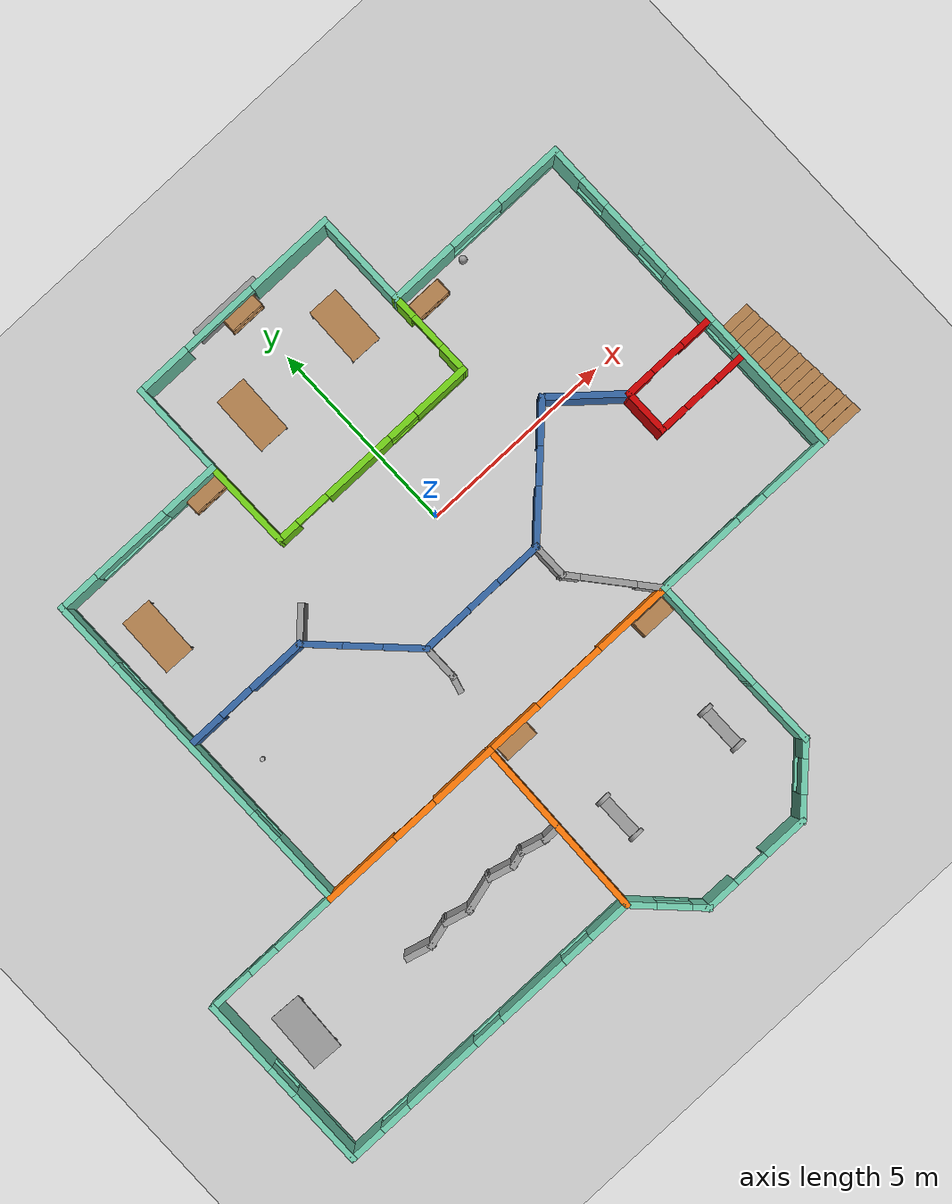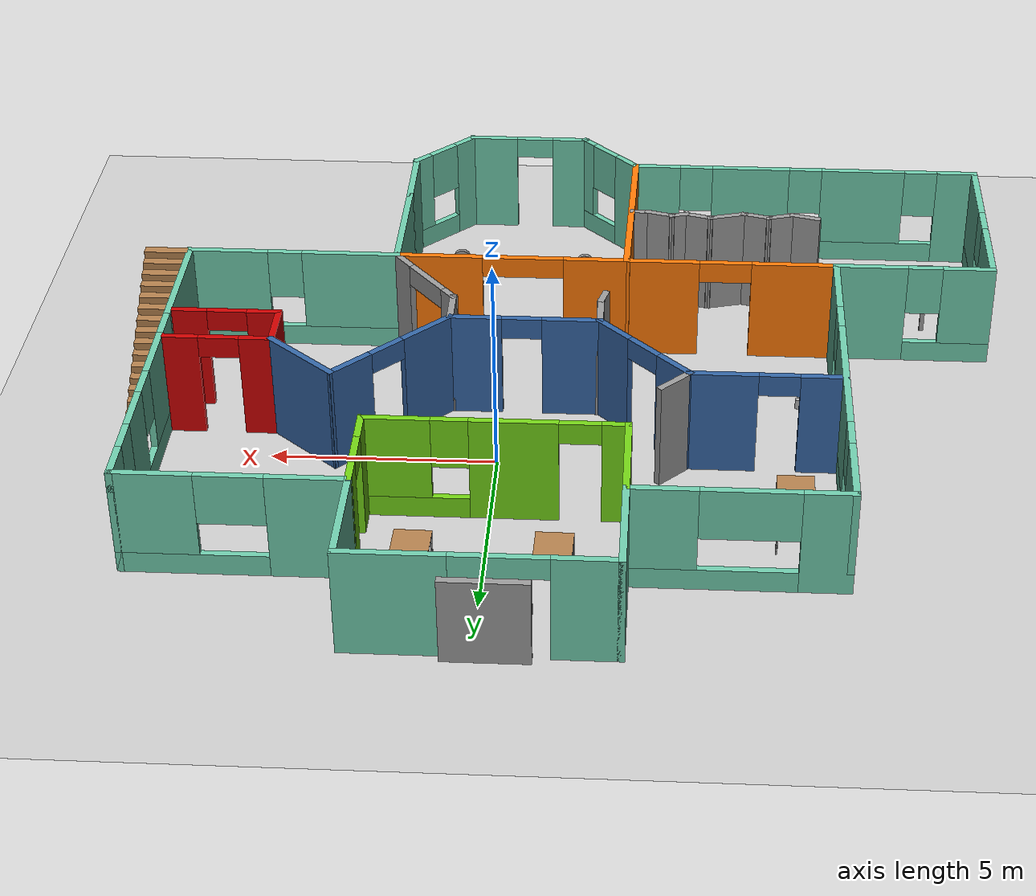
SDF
<sdf version="1.6">
 <world name="default">
  <light name="sun" type="directional">
   <pose>0 0 10 0 -0 0</pose>
   <diffuse>0.8 0.8 0.8 1</diffuse>
   <specular>0.2 0.2 0.2 1</specular>
   <attenuation>
    <range>1000</range>
    <constant>0.9</constant>
    <linear>0.01</linear>
    <quadratic>0.001</quadratic>
   </attenuation>
   <direction>-0.5 0.1 -0.9</direction>
  </light>
  <model name="ground_plane">
   <static>1</static>
   <link name="link">
    <collision name="collision">
     <geometry><plane><normal>0 0 1</normal><size>100 100</size></plane></geometry>
     <surface>
      <contact><collide_bitmask>65535</collide_bitmask></contact>
      <friction><ode><mu>100</mu><mu2>50</mu2></ode></friction>
     </surface>
    </collision>
    <visual name="visual">
     <cast_shadows>0</cast_shadows>
     <geometry><plane><normal>0 0 1</normal><size>100 100</size></plane></geometry>
     <material>
      <script><uri>file://media/materials/scripts/gazebo.material</uri><name>Gazebo/Grey</name></script>
     </material>
    </visual>
   </link>
  </model>
  <gravity>0 0 -9.8</gravity>
  <magnetic_field>6e-06 2.3e-05 -4.2e-05</magnetic_field>
  <atmosphere type="adiabatic"/>
  <physics name="default_physics" default="0" type="ode">
   <max_step_size>0.001</max_step_size>
   <real_time_factor>1</real_time_factor>
   <real_time_update_rate>1000</real_time_update_rate>
  </physics>
  <scene><ambient>0.4 0.4 0.4 1</ambient><background>0.7 0.7 0.7 1</background><shadows>1</shadows></scene>
  <spherical_coordinates>
   <surface_model>EARTH_WGS84</surface_model>
   <latitude_deg>0</latitude_deg>
   <longitude_deg>0</longitude_deg>
   <elevation>0</elevation>
   <heading_deg>0</heading_deg>
  </spherical_coordinates>
  <model name="model">
   <pose>-1.34408 -2.0758 0 0 -0 0</pose>
   <link name="Door_1">
    <collision name="Door_1_Collision">
     <geometry><box><size>1.8483 0.2 2</size></box></geometry>
     <pose>0 0 1 0 -0 0</pose>
    </collision>
    <visual name="Door_1_Visual">
     <pose>0 0 1 0 -0 0</pose>
     <geometry><box><size>1.8483 0.2 2</size></box></geometry>
     <material>
      <script><uri>file://media/materials/scripts/gazebo.material</uri><name>Gazebo/Grey</name></script>
     </material>
    </visual>
    <pose>1.0621 8.71185 0 0 -0 0</pose>
   </link>
   <link name="Stairs_0">
    <visual name="Stairs_0_Visual_0">
     <pose>9.38776 0.705751 0.083333 0 -0 0</pose>
     <geometry><box><size>1 0.233333 0.166667</size></box></geometry>
     <material>
      <script><uri>file://media/materials/scripts/gazebo.material</uri><name>Gazebo/Wood</name></script>
      <ambient>1 1 1 1</ambient>
     </material>
     <meta><layer>0</layer></meta>
    </visual>
    <collision name="Stairs_0_Collision_0">
     <geometry><box><size>1 0.233333 0.166667</size></box></geometry>
     <pose>9.38776 0.705751 0.083333 0 -0 0</pose>
    </collision>
    <visual name="Stairs_0_Visual_1">
     <pose>9.38776 0.472418 0.25 0 -0 0</pose>
     <geometry><box><size>1 0.233333 0.166667</size></box></geometry>
     <material>
      <script><uri>file://media/materials/scripts/gazebo.material</uri><name>Gazebo/Wood</name></script>
      <ambient>1 1 1 1</ambient>
     </material>
     <meta><layer>0</layer></meta>
    </visual>
    <collision name="Stairs_0_Collision_1">
     <geometry><box><size>1 0.233333 0.166667</size></box></geometry>
     <pose>9.38776 0.472418 0.25 0 -0 0</pose>
    </collision>
    <visual name="Stairs_0_Visual_2">
     <pose>9.38776 0.239084 0.416667 0 -0 0</pose>
     <geometry><box><size>1 0.233333 0.166667</size></box></geometry>
     <material>
      <script><uri>file://media/materials/scripts/gazebo.material</uri><name>Gazebo/Wood</name></script>
      <ambient>1 1 1 1</ambient>
     </material>
     <meta><layer>0</layer></meta>
    </visual>
    <collision name="Stairs_0_Collision_2">
     <geometry><box><size>1 0.233333 0.166667</size></box></geometry>
     <pose>9.38776 0.239084 0.416667 0 -0 0</pose>
    </collision>
    <visual name="Stairs_0_Visual_3">
     <pose>9.38776 0.005751 0.583333 0 -0 0</pose>
     <geometry><box><size>1 0.233333 0.166667</size></box></geometry>
     <material>
      <script><uri>file://media/materials/scripts/gazebo.material</uri><name>Gazebo/Wood</name></script>
      <ambient>1 1 1 1</ambient>
     </material>
     <meta><layer>0</layer></meta>
    </visual>
    <collision name="Stairs_0_Collision_3">
     <geometry><box><size>1 0.233333 0.166667</size></box></geometry>
     <pose>9.38776 0.005751 0.583333 0 -0 0</pose>
    </collision>
    <visual name="Stairs_0_Visual_4">
     <pose>9.38776 -0.227582 0.75 0 -0 0</pose>
     <geometry><box><size>1 0.233333 0.166667</size></box></geometry>
     <material>
      <script><uri>file://media/materials/scripts/gazebo.material</uri><name>Gazebo/Wood</name></script>
      <ambient>1 1 1 1</ambient>
     </material>
     <meta><layer>0</layer></meta>
    </visual>
    <collision name="Stairs_0_Collision_4">
     <geometry><box><size>1 0.233333 0.166667</size></box></geometry>
     <pose>9.38776 -0.227582 0.75 0 -0 0</pose>
    </collision>
    <visual name="Stairs_0_Visual_5">
     <pose>9.38776 -0.460916 0.916667 0 -0 0</pose>
     <geometry><box><size>1 0.233333 0.166667</size></box></geometry>
     <material>
      <script><uri>file://media/materials/scripts/gazebo.material</uri><name>Gazebo/Wood</name></script>
      <ambient>1 1 1 1</ambient>
     </material>
     <meta><layer>0</layer></meta>
    </visual>
    <collision name="Stairs_0_Collision_5">
     <geometry><box><size>1 0.233333 0.166667</size></box></geometry>
     <pose>9.38776 -0.460916 0.916667 0 -0 0</pose>
    </collision>
    <visual name="Stairs_0_Visual_6">
     <pose>9.38776 -0.694249 1.08333 0 -0 0</pose>
     <geometry><box><size>1 0.233333 0.166667</size></box></geometry>
     <material>
      <script><uri>file://media/materials/scripts/gazebo.material</uri><name>Gazebo/Wood</name></script>
      <ambient>1 1 1 1</ambient>
     </material>
     <meta><layer>0</layer></meta>
    </visual>
    <collision name="Stairs_0_Collision_6">
     <geometry><box><size>1 0.233333 0.166667</size></box></geometry>
     <pose>9.38776 -0.694249 1.08333 0 -0 0</pose>
    </collision>
    <visual name="Stairs_0_Visual_7">
     <pose>9.38776 -0.927582 1.25 0 -0 0</pose>
     <geometry><box><size>1 0.233333 0.166667</size></box></geometry>
     <material>
      <script><uri>file://media/materials/scripts/gazebo.material</uri><name>Gazebo/Wood</name></script>
      <ambient>1 1 1 1</ambient>
     </material>
     <meta><layer>0</layer></meta>
    </visual>
    <collision name="Stairs_0_Collision_7">
     <geometry><box><size>1 0.233333 0.166667</size></box></geometry>
     <pose>9.38776 -0.927582 1.25 0 -0 0</pose>
    </collision>
    <visual name="Stairs_0_Visual_8">
     <pose>9.38776 -1.16092 1.41667 0 -0 0</pose>
     <geometry><box><size>1 0.233333 0.166667</size></box></geometry>
     <material>
      <script><uri>file://media/materials/scripts/gazebo.material</uri><name>Gazebo/Wood</name></script>
      <ambient>1 1 1 1</ambient>
     </material>
     <meta><layer>0</layer></meta>
    </visual>
    <collision name="Stairs_0_Collision_8">
     <geometry><box><size>1 0.233333 0.166667</size></box></geometry>
     <pose>9.38776 -1.16092 1.41667 0 -0 0</pose>
    </collision>
    <visual name="Stairs_0_Visual_9">
     <pose>9.38776 -1.39425 1.58333 0 -0 0</pose>
     <geometry><box><size>1 0.233333 0.166667</size></box></geometry>
     <material>
      <script><uri>file://media/materials/scripts/gazebo.material</uri><name>Gazebo/Wood</name></script>
      <ambient>1 1 1 1</ambient>
     </material>
     <meta><layer>0</layer></meta>
    </visual>
    <collision name="Stairs_0_Collision_9">
     <geometry><box><size>1 0.233333 0.166667</size></box></geometry>
     <pose>9.38776 -1.39425 1.58333 0 -0 0</pose>
    </collision>
    <visual name="Stairs_0_Visual_10">
     <pose>9.38776 -1.62758 1.75 0 -0 0</pose>
     <geometry><box><size>1 0.233333 0.166667</size></box></geometry>
     <material>
      <script><uri>file://media/materials/scripts/gazebo.material</uri><name>Gazebo/Wood</name></script>
      <ambient>1 1 1 1</ambient>
     </material>
     <meta><layer>0</layer></meta>
    </visual>
    <collision name="Stairs_0_Collision_10">
     <geometry><box><size>1 0.233333 0.166667</size></box></geometry>
     <pose>9.38776 -1.62758 1.75 0 -0 0</pose>
    </collision>
    <visual name="Stairs_0_Visual_11">
     <pose>9.38776 -1.86092 1.91667 0 -0 0</pose>
     <geometry><box><size>1 0.233333 0.166667</size></box></geometry>
     <material>
      <script><uri>file://media/materials/scripts/gazebo.material</uri><name>Gazebo/Wood</name></script>
      <ambient>1 1 1 1</ambient>
     </material>
     <meta><layer>0</layer></meta>
    </visual>
    <collision name="Stairs_0_Collision_11">
     <geometry><box><size>1 0.233333 0.166667</size></box></geometry>
     <pose>9.38776 -1.86092 1.91667 0 -0 0</pose>
    </collision>
    <visual name="Stairs_0_Visual_12">
     <pose>9.38776 -2.09425 2.08333 0 -0 0</pose>
     <geometry><box><size>1 0.233333 0.166667</size></box></geometry>
     <material>
      <script><uri>file://media/materials/scripts/gazebo.material</uri><name>Gazebo/Wood</name></script>
      <ambient>1 1 1 1</ambient>
     </material>
     <meta><layer>0</layer></meta>
    </visual>
    <collision name="Stairs_0_Collision_12">
     <geometry><box><size>1 0.233333 0.166667</size></box></geometry>
     <pose>9.38776 -2.09425 2.08333 0 -0 0</pose>
    </collision>
    <visual name="Stairs_0_Visual_13">
     <pose>9.38776 -2.32758 2.25 0 -0 0</pose>
     <geometry><box><size>1 0.233333 0.166667</size></box></geometry>
     <material>
      <script><uri>file://media/materials/scripts/gazebo.material</uri><name>Gazebo/Wood</name></script>
      <ambient>1 1 1 1</ambient>
     </material>
     <meta><layer>0</layer></meta>
    </visual>
    <collision name="Stairs_0_Collision_13">
     <geometry><box><size>1 0.233333 0.166667</size></box></geometry>
     <pose>9.38776 -2.32758 2.25 0 -0 0</pose>
    </collision>
    <visual name="Stairs_0_Visual_14">
     <pose>9.38776 -2.56092 2.41667 0 -0 0</pose>
     <geometry><box><size>1 0.233333 0.166667</size></box></geometry>
     <material>
      <script><uri>file://media/materials/scripts/gazebo.material</uri><name>Gazebo/Wood</name></script>
      <ambient>1 1 1 1</ambient>
     </material>
     <meta><layer>0</layer></meta>
    </visual>
    <collision name="Stairs_0_Collision_14">
     <geometry><box><size>1 0.233333 0.166667</size></box></geometry>
     <pose>9.38776 -2.56092 2.41667 0 -0 0</pose>
    </collision>
   </link>
   <link name="Wall_10">
    <pose>6.41224 6.21961 0 0 -0 0</pose>
    <visual name="Wall_10_Visual_0">
     <pose>-1.6072 0 1.25 0 -0 0</pose>
     <geometry><box><size>1.78559 0.15 2.5</size></box></geometry>
     <material>
      <script><uri>file://media/materials/scripts/gazebo.material</uri><name>Gazebo/Grey</name></script>
      <ambient>0.435294 0.796078 0.67451 1</ambient>
     </material>
     <meta><layer>0</layer></meta>
    </visual>
    <collision name="Wall_10_Collision_0">
     <geometry><box><size>1.78559 0.15 2.5</size></box></geometry>
     <pose>-1.6072 0 1.25 0 -0 0</pose>
    </collision>
    <visual name="Wall_10_Visual_1">
     <pose>0.892797 0 0.25 0 -0 0</pose>
     <geometry><box><size>3.21441 0.15 0.5</size></box></geometry>
     <material>
      <script><uri>file://media/materials/scripts/gazebo.material</uri><name>Gazebo/Grey</name></script>
      <ambient>0.435294 0.796078 0.67451 1</ambient>
     </material>
     <meta><layer>0</layer></meta>
    </visual>
    <collision name="Wall_10_Collision_1">
     <geometry><box><size>3.21441 0.15 0.5</size></box></geometry>
     <pose>0.892797 0 0.25 0 -0 0</pose>
    </collision>
    <visual name="Wall_10_Visual_2">
     <pose>1.61399 0 1.5 0 -0 0</pose>
     <geometry><box><size>1.77201 0.15 2</size></box></geometry>
     <material>
      <script><uri>file://media/materials/scripts/gazebo.material</uri><name>Gazebo/Grey</name></script>
      <ambient>0.435294 0.796078 0.67451 1</ambient>
     </material>
     <meta><layer>0</layer></meta>
    </visual>
    <collision name="Wall_10_Collision_2">
     <geometry><box><size>1.77201 0.15 2</size></box></geometry>
     <pose>1.61399 0 1.5 0 -0 0</pose>
    </collision>
    <visual name="Wall_10_Visual_3">
     <pose>0.006791 0 1.9 0 -0 0</pose>
     <geometry><box><size>1.4424 0.15 1.2</size></box></geometry>
     <material>
      <script><uri>file://media/materials/scripts/gazebo.material</uri><name>Gazebo/Grey</name></script>
      <ambient>0.435294 0.796078 0.67451 1</ambient>
     </material>
     <meta><layer>0</layer></meta>
    </visual>
    <collision name="Wall_10_Collision_3">
     <geometry><box><size>1.4424 0.15 1.2</size></box></geometry>
     <pose>0.006791 0 1.9 0 -0 0</pose>
    </collision>
   </link>
   <link name="Wall_11">
    <pose>8.83724 1.79461 0 0 -0 -1.5708</pose>
    <visual name="Wall_11_Visual_0">
     <pose>-4.02485 0 1.25 0 -0 0</pose>
     <geometry><box><size>0.950301 0.15 2.5</size></box></geometry>
     <material>
      <script><uri>file://media/materials/scripts/gazebo.material</uri><name>Gazebo/Grey</name></script>
      <ambient>0.435294 0.796078 0.67451 1</ambient>
     </material>
     <meta><layer>0</layer></meta>
    </visual>
    <collision name="Wall_11_Collision_0">
     <geometry><box><size>0.950301 0.15 2.5</size></box></geometry>
     <pose>-4.02485 0 1.25 0 -0 0</pose>
    </collision>
    <visual name="Wall_11_Visual_1">
     <pose>0.47515 0 0.25 0 -0 0</pose>
     <geometry><box><size>8.0497 0.15 0.5</size></box></geometry>
     <material>
      <script><uri>file://media/materials/scripts/gazebo.material</uri><name>Gazebo/Grey</name></script>
      <ambient>0.435294 0.796078 0.67451 1</ambient>
     </material>
     <meta><layer>0</layer></meta>
    </visual>
    <collision name="Wall_11_Collision_1">
     <geometry><box><size>8.0497 0.15 0.5</size></box></geometry>
     <pose>0.47515 0 0.25 0 -0 0</pose>
    </collision>
    <visual name="Wall_11_Visual_2">
     <pose>-2.14022 0 1.5 0 -0 0</pose>
     <geometry><box><size>1.21896 0.15 2</size></box></geometry>
     <material>
      <script><uri>file://media/materials/scripts/gazebo.material</uri><name>Gazebo/Grey</name></script>
      <ambient>0.435294 0.796078 0.67451 1</ambient>
     </material>
     <meta><layer>0</layer></meta>
    </visual>
    <collision name="Wall_11_Collision_2">
     <geometry><box><size>1.21896 0.15 2</size></box></geometry>
     <pose>-2.14022 0 1.5 0 -0 0</pose>
    </collision>
    <visual name="Wall_11_Visual_3">
     <pose>0.031685 0 1.5 0 -0 0</pose>
     <geometry><box><size>1.52486 0.15 2</size></box></geometry>
     <material>
      <script><uri>file://media/materials/scripts/gazebo.material</uri><name>Gazebo/Grey</name></script>
      <ambient>0.435294 0.796078 0.67451 1</ambient>
     </material>
     <meta><layer>0</layer></meta>
    </visual>
    <collision name="Wall_11_Collision_3">
     <geometry><box><size>1.52486 0.15 2</size></box></geometry>
     <pose>0.031685 0 1.5 0 -0 0</pose>
    </collision>
    <visual name="Wall_11_Visual_4">
     <pose>3.04706 0 1.5 0 -0 0</pose>
     <geometry><box><size>2.90589 0.15 2</size></box></geometry>
     <material>
      <script><uri>file://media/materials/scripts/gazebo.material</uri><name>Gazebo/Grey</name></script>
      <ambient>0.435294 0.796078 0.67451 1</ambient>
     </material>
     <meta><layer>0</layer></meta>
    </visual>
    <collision name="Wall_11_Collision_4">
     <geometry><box><size>2.90589 0.15 2</size></box></geometry>
     <pose>3.04706 0 1.5 0 -0 0</pose>
    </collision>
    <visual name="Wall_11_Visual_5">
     <pose>-3.1497 0 1.9 0 -0 0</pose>
     <geometry><box><size>0.8 0.15 1.2</size></box></geometry>
     <material>
      <script><uri>file://media/materials/scripts/gazebo.material</uri><name>Gazebo/Grey</name></script>
      <ambient>0.435294 0.796078 0.67451 1</ambient>
     </material>
     <meta><layer>0</layer></meta>
    </visual>
    <collision name="Wall_11_Collision_5">
     <geometry><box><size>0.8 0.15 1.2</size></box></geometry>
     <pose>-3.1497 0 1.9 0 -0 0</pose>
    </collision>
    <visual name="Wall_11_Visual_6">
     <pose>-1.13074 0 1.9 0 -0 0</pose>
     <geometry><box><size>0.8 0.15 1.2</size></box></geometry>
     <material>
      <script><uri>file://media/materials/scripts/gazebo.material</uri><name>Gazebo/Grey</name></script>
      <ambient>0.435294 0.796078 0.67451 1</ambient>
     </material>
     <meta><layer>0</layer></meta>
    </visual>
    <collision name="Wall_11_Collision_6">
     <geometry><box><size>0.8 0.15 1.2</size></box></geometry>
     <pose>-1.13074 0 1.9 0 -0 0</pose>
    </collision>
    <visual name="Wall_11_Visual_7">
     <pose>1.19411 0 1.9 0 -0 0</pose>
     <geometry><box><size>0.8 0.15 1.2</size></box></geometry>
     <material>
      <script><uri>file://media/materials/scripts/gazebo.material</uri><name>Gazebo/Grey</name></script>
      <ambient>0.435294 0.796078 0.67451 1</ambient>
     </material>
     <meta><layer>0</layer></meta>
    </visual>
    <collision name="Wall_11_Collision_7">
     <geometry><box><size>0.8 0.15 1.2</size></box></geometry>
     <pose>1.19411 0 1.9 0 -0 0</pose>
    </collision>
   </link>
   <link name="Wall_12">
    <pose>6.41224 -2.63039 0 0 -0 3.14159</pose>
    <visual name="Wall_12_Visual_0">
     <pose>-1.55241 0 1.25 0 -0 0</pose>
     <geometry><box><size>1.89517 0.15 2.5</size></box></geometry>
     <material>
      <script><uri>file://media/materials/scripts/gazebo.material</uri><name>Gazebo/Grey</name></script>
      <ambient>0.435294 0.796078 0.67451 1</ambient>
     </material>
     <meta><layer>0</layer></meta>
    </visual>
    <collision name="Wall_12_Collision_0">
     <geometry><box><size>1.89517 0.15 2.5</size></box></geometry>
     <pose>-1.55241 0 1.25 0 -0 0</pose>
    </collision>
    <visual name="Wall_12_Visual_1">
     <pose>0.947587 0 0.25 0 -0 0</pose>
     <geometry><box><size>3.10483 0.15 0.5</size></box></geometry>
     <material>
      <script><uri>file://media/materials/scripts/gazebo.material</uri><name>Gazebo/Grey</name></script>
      <ambient>0.435294 0.796078 0.67451 1</ambient>
     </material>
     <meta><layer>0</layer></meta>
    </visual>
    <collision name="Wall_12_Collision_1">
     <geometry><box><size>3.10483 0.15 0.5</size></box></geometry>
     <pose>0.947587 0 0.25 0 -0 0</pose>
    </collision>
    <visual name="Wall_12_Visual_2">
     <pose>1.34759 0 1.5 0 -0 0</pose>
     <geometry><box><size>2.30483 0.15 2</size></box></geometry>
     <material>
      <script><uri>file://media/materials/scripts/gazebo.material</uri><name>Gazebo/Grey</name></script>
      <ambient>0.435294 0.796078 0.67451 1</ambient>
     </material>
     <meta><layer>0</layer></meta>
    </visual>
    <collision name="Wall_12_Collision_2">
     <geometry><box><size>2.30483 0.15 2</size></box></geometry>
     <pose>1.34759 0 1.5 0 -0 0</pose>
    </collision>
    <visual name="Wall_12_Visual_3">
     <pose>-0.204827 0 1.9 0 -0 0</pose>
     <geometry><box><size>0.8 0.15 1.2</size></box></geometry>
     <material>
      <script><uri>file://media/materials/scripts/gazebo.material</uri><name>Gazebo/Grey</name></script>
      <ambient>0.435294 0.796078 0.67451 1</ambient>
     </material>
     <meta><layer>0</layer></meta>
    </visual>
    <collision name="Wall_12_Collision_3">
     <geometry><box><size>0.8 0.15 1.2</size></box></geometry>
     <pose>-0.204827 0 1.9 0 -0 0</pose>
    </collision>
   </link>
   <link name="Wall_13">
    <collision name="Wall_13_Collision">
     <geometry><box><size>3 0.15 2.5</size></box></geometry>
     <pose>0 0 1.25 0 -0 0</pose>
    </collision>
    <visual name="Wall_13_Visual">
     <pose>0 0 1.25 0 -0 0</pose>
     <geometry><box><size>3 0.15 2.5</size></box></geometry>
     <material>
      <script><uri>file://media/materials/scripts/gazebo.material</uri><name>Gazebo/Grey</name></script>
      <ambient>0.435294 0.796078 0.67451 1</ambient>
     </material>
     <meta><layer>0</layer></meta>
    </visual>
    <pose>3.98724 -4.05539 0 0 -0 -1.5708</pose>
   </link>
   <link name="Wall_16">
    <pose>-3.78776 -2.63039 0 0 -0 3.14159</pose>
    <visual name="Wall_16_Visual_0">
     <pose>-1.61733 0 1.25 0 -0 0</pose>
     <geometry><box><size>1.76534 0.15 2.5</size></box></geometry>
     <material>
      <script><uri>file://media/materials/scripts/gazebo.material</uri><name>Gazebo/Grey</name></script>
      <ambient>0.996078 0.47451 0.0196078 1</ambient>
     </material>
     <meta><layer>0</layer></meta>
    </visual>
    <collision name="Wall_16_Collision_0">
     <geometry><box><size>1.76534 0.15 2.5</size></box></geometry>
     <pose>-1.61733 0 1.25 0 -0 0</pose>
    </collision>
    <visual name="Wall_16_Visual_1">
     <pose>1.48562 0 1.25 0 -0 0</pose>
     <geometry><box><size>2.02876 0.15 2.5</size></box></geometry>
     <material>
      <script><uri>file://media/materials/scripts/gazebo.material</uri><name>Gazebo/Grey</name></script>
      <ambient>0.996078 0.47451 0.0196078 1</ambient>
     </material>
     <meta><layer>0</layer></meta>
    </visual>
    <collision name="Wall_16_Collision_1">
     <geometry><box><size>2.02876 0.15 2.5</size></box></geometry>
     <pose>1.48562 0 1.25 0 -0 0</pose>
    </collision>
    <visual name="Wall_16_Visual_2">
     <pose>-0.131714 0 2.25 0 -0 0</pose>
     <geometry><box><size>1.2059 0.15 0.5</size></box></geometry>
     <material>
      <script><uri>file://media/materials/scripts/gazebo.material</uri><name>Gazebo/Grey</name></script>
      <ambient>0.996078 0.47451 0.0196078 1</ambient>
     </material>
     <meta><layer>0</layer></meta>
    </visual>
    <collision name="Wall_16_Collision_2">
     <geometry><box><size>1.2059 0.15 0.5</size></box></geometry>
     <pose>-0.131714 0 2.25 0 -0 0</pose>
    </collision>
   </link>
   <link name="Wall_17">
    <pose>-6.21276 1.79461 0 0 -0 1.5708</pose>
    <visual name="Wall_17_Visual_0">
     <pose>-3.56709 0 1.25 0 -0 0</pose>
     <geometry><box><size>1.86582 0.15 2.5</size></box></geometry>
     <material>
      <script><uri>file://media/materials/scripts/gazebo.material</uri><name>Gazebo/Grey</name></script>
      <ambient>0.435294 0.796078 0.67451 1</ambient>
     </material>
     <meta><layer>0</layer></meta>
    </visual>
    <collision name="Wall_17_Collision_0">
     <geometry><box><size>1.86582 0.15 2.5</size></box></geometry>
     <pose>-3.56709 0 1.25 0 -0 0</pose>
    </collision>
    <visual name="Wall_17_Visual_1">
     <pose>0.932909 0 0.25 0 -0 0</pose>
     <geometry><box><size>7.13418 0.15 0.5</size></box></geometry>
     <material>
      <script><uri>file://media/materials/scripts/gazebo.material</uri><name>Gazebo/Grey</name></script>
      <ambient>0.435294 0.796078 0.67451 1</ambient>
     </material>
     <meta><layer>0</layer></meta>
    </visual>
    <collision name="Wall_17_Collision_1">
     <geometry><box><size>7.13418 0.15 0.5</size></box></geometry>
     <pose>0.932909 0 0.25 0 -0 0</pose>
    </collision>
    <visual name="Wall_17_Visual_2">
     <pose>0.029496 0 1.5 0 -0 0</pose>
     <geometry><box><size>3.72735 0.15 2</size></box></geometry>
     <material>
      <script><uri>file://media/materials/scripts/gazebo.material</uri><name>Gazebo/Grey</name></script>
      <ambient>0.435294 0.796078 0.67451 1</ambient>
     </material>
     <meta><layer>0</layer></meta>
    </visual>
    <collision name="Wall_17_Collision_2">
     <geometry><box><size>3.72735 0.15 2</size></box></geometry>
     <pose>0.029496 0 1.5 0 -0 0</pose>
    </collision>
    <visual name="Wall_17_Visual_3">
     <pose>3.59659 0 1.5 0 -0 0</pose>
     <geometry><box><size>1.80683 0.15 2</size></box></geometry>
     <material>
      <script><uri>file://media/materials/scripts/gazebo.material</uri><name>Gazebo/Grey</name></script>
      <ambient>0.435294 0.796078 0.67451 1</ambient>
     </material>
     <meta><layer>0</layer></meta>
    </visual>
    <collision name="Wall_17_Collision_3">
     <geometry><box><size>1.80683 0.15 2</size></box></geometry>
     <pose>3.59659 0 1.5 0 -0 0</pose>
    </collision>
    <visual name="Wall_17_Visual_4">
     <pose>-2.23418 0 1.9 0 -0 0</pose>
     <geometry><box><size>0.8 0.15 1.2</size></box></geometry>
     <material>
      <script><uri>file://media/materials/scripts/gazebo.material</uri><name>Gazebo/Grey</name></script>
      <ambient>0.435294 0.796078 0.67451 1</ambient>
     </material>
     <meta><layer>0</layer></meta>
    </visual>
    <collision name="Wall_17_Collision_4">
     <geometry><box><size>0.8 0.15 1.2</size></box></geometry>
     <pose>-2.23418 0 1.9 0 -0 0</pose>
    </collision>
    <visual name="Wall_17_Visual_5">
     <pose>2.29317 0 1.9 0 -0 0</pose>
     <geometry><box><size>0.8 0.15 1.2</size></box></geometry>
     <material>
      <script><uri>file://media/materials/scripts/gazebo.material</uri><name>Gazebo/Grey</name></script>
      <ambient>0.435294 0.796078 0.67451 1</ambient>
     </material>
     <meta><layer>0</layer></meta>
    </visual>
    <collision name="Wall_17_Collision_5">
     <geometry><box><size>0.8 0.15 1.2</size></box></geometry>
     <pose>2.29317 0 1.9 0 -0 0</pose>
    </collision>
   </link>
   <link name="Wall_21">
    <pose>-4.53435 2.02213 0 0 -0 0</pose>
    <visual name="Wall_21_Visual_0">
     <pose>-1.22897 0 1.25 0 -0 0</pose>
     <geometry><box><size>1.04206 0.15 2.5</size></box></geometry>
     <material>
      <script><uri>file://media/materials/scripts/gazebo.material</uri><name>Gazebo/Grey</name></script>
      <ambient>0.203922 0.396078 0.643137 1</ambient>
     </material>
     <meta><layer>0</layer></meta>
    </visual>
    <collision name="Wall_21_Collision_0">
     <geometry><box><size>1.04206 0.15 2.5</size></box></geometry>
     <pose>-1.22897 0 1.25 0 -0 0</pose>
    </collision>
    <visual name="Wall_21_Visual_1">
     <pose>0.971028 0 1.25 0 -0 0</pose>
     <geometry><box><size>1.55794 0.15 2.5</size></box></geometry>
     <material>
      <script><uri>file://media/materials/scripts/gazebo.material</uri><name>Gazebo/Grey</name></script>
      <ambient>0.203922 0.396078 0.643137 1</ambient>
     </material>
     <meta><layer>0</layer></meta>
    </visual>
    <collision name="Wall_21_Collision_1">
     <geometry><box><size>1.55794 0.15 2.5</size></box></geometry>
     <pose>0.971028 0 1.25 0 -0 0</pose>
    </collision>
    <visual name="Wall_21_Visual_2">
     <pose>-0.257943 0 2.25 0 -0 0</pose>
     <geometry><box><size>0.9 0.15 0.5</size></box></geometry>
     <material>
      <script><uri>file://media/materials/scripts/gazebo.material</uri><name>Gazebo/Grey</name></script>
      <ambient>0.203922 0.396078 0.643137 1</ambient>
     </material>
     <meta><layer>0</layer></meta>
    </visual>
    <collision name="Wall_21_Collision_2">
     <geometry><box><size>0.9 0.15 0.5</size></box></geometry>
     <pose>-0.257943 0 2.25 0 -0 0</pose>
    </collision>
   </link>
   <link name="Wall_28">
    <pose>-1.85172 1.0145 0 0 -0 -0.785398</pose>
    <visual name="Wall_28_Visual_0">
     <pose>-0.981423 0 1.25 0 -0 0</pose>
     <geometry><box><size>1.03716 0.15 2.5</size></box></geometry>
     <material>
      <script><uri>file://media/materials/scripts/gazebo.material</uri><name>Gazebo/Grey</name></script>
      <ambient>0.203922 0.396078 0.643137 1</ambient>
     </material>
     <meta><layer>0</layer></meta>
    </visual>
    <collision name="Wall_28_Collision_0">
     <geometry><box><size>1.03716 0.15 2.5</size></box></geometry>
     <pose>-0.981423 0 1.25 0 -0 0</pose>
    </collision>
    <visual name="Wall_28_Visual_1">
     <pose>0.968577 0 1.25 0 -0 0</pose>
     <geometry><box><size>1.06285 0.15 2.5</size></box></geometry>
     <material>
      <script><uri>file://media/materials/scripts/gazebo.material</uri><name>Gazebo/Grey</name></script>
      <ambient>0.203922 0.396078 0.643137 1</ambient>
     </material>
     <meta><layer>0</layer></meta>
    </visual>
    <collision name="Wall_28_Collision_1">
     <geometry><box><size>1.06285 0.15 2.5</size></box></geometry>
     <pose>0.968577 0 1.25 0 -0 0</pose>
    </collision>
    <visual name="Wall_28_Visual_2">
     <pose>-0.012845 0 2.25 0 -0 0</pose>
     <geometry><box><size>0.9 0.15 0.5</size></box></geometry>
     <material>
      <script><uri>file://media/materials/scripts/gazebo.material</uri><name>Gazebo/Grey</name></script>
      <ambient>0.203922 0.396078 0.643137 1</ambient>
     </material>
     <meta><layer>0</layer></meta>
    </visual>
    <collision name="Wall_28_Collision_2">
     <geometry><box><size>0.9 0.15 0.5</size></box></geometry>
     <pose>-0.012845 0 2.25 0 -0 0</pose>
    </collision>
   </link>
   <link name="Wall_31">
    <pose>0.83091 0.006871 0 0 -0 0</pose>
    <visual name="Wall_31_Visual_0">
     <pose>-1.06671 0 1.25 0 -0 0</pose>
     <geometry><box><size>1.36658 0.15 2.5</size></box></geometry>
     <material>
      <script><uri>file://media/materials/scripts/gazebo.material</uri><name>Gazebo/Grey</name></script>
      <ambient>0.203922 0.396078 0.643137 1</ambient>
     </material>
     <meta><layer>0</layer></meta>
    </visual>
    <collision name="Wall_31_Collision_0">
     <geometry><box><size>1.36658 0.15 2.5</size></box></geometry>
     <pose>-1.06671 0 1.25 0 -0 0</pose>
    </collision>
    <visual name="Wall_31_Visual_1">
     <pose>1.13329 0 1.25 0 -0 0</pose>
     <geometry><box><size>1.23341 0.15 2.5</size></box></geometry>
     <material>
      <script><uri>file://media/materials/scripts/gazebo.material</uri><name>Gazebo/Grey</name></script>
      <ambient>0.203922 0.396078 0.643137 1</ambient>
     </material>
     <meta><layer>0</layer></meta>
    </visual>
    <collision name="Wall_31_Collision_1">
     <geometry><box><size>1.23341 0.15 2.5</size></box></geometry>
     <pose>1.13329 0 1.25 0 -0 0</pose>
    </collision>
    <visual name="Wall_31_Visual_2">
     <pose>0.066585 0 2.25 0 -0 0</pose>
     <geometry><box><size>0.9 0.15 0.5</size></box></geometry>
     <material>
      <script><uri>file://media/materials/scripts/gazebo.material</uri><name>Gazebo/Grey</name></script>
      <ambient>0.203922 0.396078 0.643137 1</ambient>
     </material>
     <meta><layer>0</layer></meta>
    </visual>
    <collision name="Wall_31_Collision_2">
     <geometry><box><size>0.9 0.15 0.5</size></box></geometry>
     <pose>0.066585 0 2.25 0 -0 0</pose>
    </collision>
   </link>
   <link name="Wall_35">
    <pose>3.69031 1.19128 0 0 -0 0.785398</pose>
    <visual name="Wall_35_Visual_0">
     <pose>-1.02961 0 1.25 0 -0 0</pose>
     <geometry><box><size>1.44079 0.15 2.5</size></box></geometry>
     <material>
      <script><uri>file://media/materials/scripts/gazebo.material</uri><name>Gazebo/Grey</name></script>
      <ambient>0.203922 0.396078 0.643137 1</ambient>
     </material>
     <meta><layer>0</layer></meta>
    </visual>
    <collision name="Wall_35_Collision_0">
     <geometry><box><size>1.44079 0.15 2.5</size></box></geometry>
     <pose>-1.02961 0 1.25 0 -0 0</pose>
    </collision>
    <visual name="Wall_35_Visual_1">
     <pose>1.17039 0 1.25 0 -0 0</pose>
     <geometry><box><size>1.15921 0.15 2.5</size></box></geometry>
     <material>
      <script><uri>file://media/materials/scripts/gazebo.material</uri><name>Gazebo/Grey</name></script>
      <ambient>0.203922 0.396078 0.643137 1</ambient>
     </material>
     <meta><layer>0</layer></meta>
    </visual>
    <collision name="Wall_35_Collision_1">
     <geometry><box><size>1.15921 0.15 2.5</size></box></geometry>
     <pose>1.17039 0 1.25 0 -0 0</pose>
    </collision>
    <visual name="Wall_35_Visual_2">
     <pose>0.140787 0 2.25 0 -0 0</pose>
     <geometry><box><size>0.9 0.15 0.5</size></box></geometry>
     <material>
      <script><uri>file://media/materials/scripts/gazebo.material</uri><name>Gazebo/Grey</name></script>
      <ambient>0.203922 0.396078 0.643137 1</ambient>
     </material>
     <meta><layer>0</layer></meta>
    </visual>
    <collision name="Wall_35_Collision_2">
     <geometry><box><size>0.9 0.15 0.5</size></box></geometry>
     <pose>0.140787 0 2.25 0 -0 0</pose>
    </collision>
   </link>
   <link name="Wall_37">
    <pose>1.19907 4.02731 0 0 -0 0</pose>
    <visual name="Wall_37_Visual_0">
     <pose>-2.56055 0 1.25 0 -0 0</pose>
     <geometry><box><size>0.628904 0.15 2.5</size></box></geometry>
     <material>
      <script><uri>file://media/materials/scripts/gazebo.material</uri><name>Gazebo/Grey</name></script>
      <ambient>0.45098 0.823529 0.0862745 1</ambient>
     </material>
     <meta><layer>0</layer></meta>
    </visual>
    <collision name="Wall_37_Collision_0">
     <geometry><box><size>0.628904 0.15 2.5</size></box></geometry>
     <pose>-2.56055 0 1.25 0 -0 0</pose>
    </collision>
    <visual name="Wall_37_Visual_1">
     <pose>-0.397199 0 1.25 0 -0 0</pose>
     <geometry><box><size>1.89779 0.15 2.5</size></box></geometry>
     <material>
      <script><uri>file://media/materials/scripts/gazebo.material</uri><name>Gazebo/Grey</name></script>
      <ambient>0.45098 0.823529 0.0862745 1</ambient>
     </material>
     <meta><layer>0</layer></meta>
    </visual>
    <collision name="Wall_37_Collision_1">
     <geometry><box><size>1.89779 0.15 2.5</size></box></geometry>
     <pose>-0.397199 0 1.25 0 -0 0</pose>
    </collision>
    <visual name="Wall_37_Visual_2">
     <pose>1.71335 0 0.25 0 -0 0</pose>
     <geometry><box><size>2.3233 0.15 0.5</size></box></geometry>
     <material>
      <script><uri>file://media/materials/scripts/gazebo.material</uri><name>Gazebo/Grey</name></script>
      <ambient>0.45098 0.823529 0.0862745 1</ambient>
     </material>
     <meta><layer>0</layer></meta>
    </visual>
    <collision name="Wall_37_Collision_2">
     <geometry><box><size>2.3233 0.15 0.5</size></box></geometry>
     <pose>1.71335 0 0.25 0 -0 0</pose>
    </collision>
    <visual name="Wall_37_Visual_3">
     <pose>2.11335 0 1.5 0 -0 0</pose>
     <geometry><box><size>1.5233 0.15 2</size></box></geometry>
     <material>
      <script><uri>file://media/materials/scripts/gazebo.material</uri><name>Gazebo/Grey</name></script>
      <ambient>0.45098 0.823529 0.0862745 1</ambient>
     </material>
     <meta><layer>0</layer></meta>
    </visual>
    <collision name="Wall_37_Collision_3">
     <geometry><box><size>1.5233 0.15 2</size></box></geometry>
     <pose>2.11335 0 1.5 0 -0 0</pose>
    </collision>
    <visual name="Wall_37_Visual_4">
     <pose>0.951698 0 1.9 0 -0 0</pose>
     <geometry><box><size>0.8 0.15 1.2</size></box></geometry>
     <material>
      <script><uri>file://media/materials/scripts/gazebo.material</uri><name>Gazebo/Grey</name></script>
      <ambient>0.45098 0.823529 0.0862745 1</ambient>
     </material>
     <meta><layer>0</layer></meta>
    </visual>
    <collision name="Wall_37_Collision_4">
     <geometry><box><size>0.8 0.15 1.2</size></box></geometry>
     <pose>0.951698 0 1.9 0 -0 0</pose>
    </collision>
    <visual name="Wall_37_Visual_5">
     <pose>-1.7961 0 2.25 0 -0 0</pose>
     <geometry><box><size>0.9 0.15 0.5</size></box></geometry>
     <material>
      <script><uri>file://media/materials/scripts/gazebo.material</uri><name>Gazebo/Grey</name></script>
      <ambient>0.45098 0.823529 0.0862745 1</ambient>
     </material>
     <meta><layer>0</layer></meta>
    </visual>
    <collision name="Wall_37_Collision_5">
     <geometry><box><size>0.9 0.15 0.5</size></box></geometry>
     <pose>-1.7961 0 2.25 0 -0 0</pose>
    </collision>
   </link>
   <link name="Wall_38">
    <pose>3.99316 5.12346 0 0 -0 1.57619</pose>
    <visual name="Wall_38_Visual_0">
     <pose>-0.775994 0 1.25 0 -0 0</pose>
     <geometry><box><size>0.790336 0.15 2.5</size></box></geometry>
     <material>
      <script><uri>file://media/materials/scripts/gazebo.material</uri><name>Gazebo/Grey</name></script>
      <ambient>0.45098 0.823529 0.0862745 1</ambient>
     </material>
     <meta><layer>0</layer></meta>
    </visual>
    <collision name="Wall_38_Collision_0">
     <geometry><box><size>0.790336 0.15 2.5</size></box></geometry>
     <pose>-0.775994 0 1.25 0 -0 0</pose>
    </collision>
    <visual name="Wall_38_Visual_1">
     <pose>0.845168 0 1.25 0 -0 0</pose>
     <geometry><box><size>0.651988 0.15 2.5</size></box></geometry>
     <material>
      <script><uri>file://media/materials/scripts/gazebo.material</uri><name>Gazebo/Grey</name></script>
      <ambient>0.45098 0.823529 0.0862745 1</ambient>
     </material>
     <meta><layer>0</layer></meta>
    </visual>
    <collision name="Wall_38_Collision_1">
     <geometry><box><size>0.651988 0.15 2.5</size></box></geometry>
     <pose>0.845168 0 1.25 0 -0 0</pose>
    </collision>
    <visual name="Wall_38_Visual_2">
     <pose>0.069174 0 2.25 0 -0 0</pose>
     <geometry><box><size>0.9 0.15 0.5</size></box></geometry>
     <material>
      <script><uri>file://media/materials/scripts/gazebo.material</uri><name>Gazebo/Grey</name></script>
      <ambient>0.45098 0.823529 0.0862745 1</ambient>
     </material>
     <meta><layer>0</layer></meta>
    </visual>
    <collision name="Wall_38_Collision_2">
     <geometry><box><size>0.9 0.15 0.5</size></box></geometry>
     <pose>0.069174 0 2.25 0 -0 0</pose>
    </collision>
   </link>
   <link name="Wall_40">
    <pose>7.52447 1.10748 0 0 -0 0</pose>
    <visual name="Wall_40_Visual_0">
     <pose>-0.852595 0 1.25 0 -0 0</pose>
     <geometry><box><size>0.794811 0.15 2.5</size></box></geometry>
     <material>
      <script><uri>file://media/materials/scripts/gazebo.material</uri><name>Gazebo/Grey</name></script>
      <ambient>0.8 0 0 1</ambient>
     </material>
     <meta><layer>0</layer></meta>
    </visual>
    <collision name="Wall_40_Collision_0">
     <geometry><box><size>0.794811 0.15 2.5</size></box></geometry>
     <pose>-0.852595 0 1.25 0 -0 0</pose>
    </collision>
    <visual name="Wall_40_Visual_1">
     <pose>0.847405 0 1.25 0 -0 0</pose>
     <geometry><box><size>0.805189 0.15 2.5</size></box></geometry>
     <material>
      <script><uri>file://media/materials/scripts/gazebo.material</uri><name>Gazebo/Grey</name></script>
      <ambient>0.8 0 0 1</ambient>
     </material>
     <meta><layer>0</layer></meta>
    </visual>
    <collision name="Wall_40_Collision_1">
     <geometry><box><size>0.805189 0.15 2.5</size></box></geometry>
     <pose>0.847405 0 1.25 0 -0 0</pose>
    </collision>
    <visual name="Wall_40_Visual_2">
     <pose>-0.005189 0 2.25 0 -0 0</pose>
     <geometry><box><size>0.9 0.15 0.5</size></box></geometry>
     <material>
      <script><uri>file://media/materials/scripts/gazebo.material</uri><name>Gazebo/Grey</name></script>
      <ambient>0.8 0 0 1</ambient>
     </material>
     <meta><layer>0</layer></meta>
    </visual>
    <collision name="Wall_40_Collision_2">
     <geometry><box><size>0.9 0.15 0.5</size></box></geometry>
     <pose>-0.005189 0 2.25 0 -0 0</pose>
    </collision>
   </link>
   <link name="Wall_42">
    <collision name="Wall_42_Collision">
     <geometry><box><size>1.25 0.15 2.5</size></box></geometry>
     <pose>0 0 1.25 0 -0 0</pose>
    </collision>
    <visual name="Wall_42_Visual">
     <pose>0 0 1.25 0 -0 0</pose>
     <geometry><box><size>1.25 0.15 2.5</size></box></geometry>
     <material>
      <script><uri>file://media/materials/scripts/gazebo.material</uri><name>Gazebo/Grey</name></script>
      <ambient>0.8 0 0 1</ambient>
     </material>
     <meta><layer>0</layer></meta>
    </visual>
    <pose>6.34947 0.557478 0 0 -0 -1.5708</pose>
   </link>
   <link name="Wall_43">
    <pose>7.52447 0.007478 0 0 -0 0</pose>
    <visual name="Wall_43_Visual_0">
     <pose>-0.852595 0 1.25 0 -0 0</pose>
     <geometry><box><size>0.794811 0.15 2.5</size></box></geometry>
     <material>
      <script><uri>file://media/materials/scripts/gazebo.material</uri><name>Gazebo/Grey</name></script>
      <ambient>0.8 0 0 1</ambient>
     </material>
     <meta><layer>0</layer></meta>
    </visual>
    <collision name="Wall_43_Collision_0">
     <geometry><box><size>0.794811 0.15 2.5</size></box></geometry>
     <pose>-0.852595 0 1.25 0 -0 0</pose>
    </collision>
    <visual name="Wall_43_Visual_1">
     <pose>0.847405 0 1.25 0 -0 0</pose>
     <geometry><box><size>0.805189 0.15 2.5</size></box></geometry>
     <material>
      <script><uri>file://media/materials/scripts/gazebo.material</uri><name>Gazebo/Grey</name></script>
      <ambient>0.8 0 0 1</ambient>
     </material>
     <meta><layer>0</layer></meta>
    </visual>
    <collision name="Wall_43_Collision_1">
     <geometry><box><size>0.805189 0.15 2.5</size></box></geometry>
     <pose>0.847405 0 1.25 0 -0 0</pose>
    </collision>
    <visual name="Wall_43_Visual_2">
     <pose>-0.005189 0 2.25 0 -0 0</pose>
     <geometry><box><size>0.9 0.15 0.5</size></box></geometry>
     <material>
      <script><uri>file://media/materials/scripts/gazebo.material</uri><name>Gazebo/Grey</name></script>
      <ambient>0.8 0 0 1</ambient>
     </material>
     <meta><layer>0</layer></meta>
    </visual>
    <collision name="Wall_43_Collision_2">
     <geometry><box><size>0.9 0.15 0.5</size></box></geometry>
     <pose>-0.005189 0 2.25 0 -0 0</pose>
    </collision>
   </link>
   <link name="Wall_45">
    <collision name="Wall_45_Collision">
     <geometry><box><size>2.09505 0.15 2.5</size></box></geometry>
     <pose>0 0 1.25 0 -0 0</pose>
    </collision>
    <visual name="Wall_45_Visual">
     <pose>0 0 1.25 0 -0 0</pose>
     <geometry><box><size>2.09505 0.15 2.5</size></box></geometry>
     <material>
      <script><uri>file://media/materials/scripts/gazebo.material</uri><name>Gazebo/Grey</name></script>
      <ambient>0.203922 0.396078 0.643137 1</ambient>
     </material>
     <meta><layer>0</layer></meta>
    </visual>
    <pose>5.6121 1.74158 0 0 -0 2.43136</pose>
   </link>
   <link name="Wall_47">
    <pose>-8.01276 -2.63039 0 0 -0 3.14159</pose>
    <visual name="Wall_47_Visual_0">
     <pose>-1.00859 0 1.25 0 -0 0</pose>
     <geometry><box><size>1.73283 0.15 2.5</size></box></geometry>
     <material>
      <script><uri>file://media/materials/scripts/gazebo.material</uri><name>Gazebo/Grey</name></script>
      <ambient>0.435294 0.796078 0.67451 1</ambient>
     </material>
     <meta><layer>0</layer></meta>
    </visual>
    <collision name="Wall_47_Collision_0">
     <geometry><box><size>1.73283 0.15 2.5</size></box></geometry>
     <pose>-1.00859 0 1.25 0 -0 0</pose>
    </collision>
    <visual name="Wall_47_Visual_1">
     <pose>0.866413 0 0.25 0 -0 0</pose>
     <geometry><box><size>2.01717 0.15 0.5</size></box></geometry>
     <material>
      <script><uri>file://media/materials/scripts/gazebo.material</uri><name>Gazebo/Grey</name></script>
      <ambient>0.435294 0.796078 0.67451 1</ambient>
     </material>
     <meta><layer>0</layer></meta>
    </visual>
    <collision name="Wall_47_Collision_1">
     <geometry><box><size>2.01717 0.15 0.5</size></box></geometry>
     <pose>0.866413 0 0.25 0 -0 0</pose>
    </collision>
    <visual name="Wall_47_Visual_2">
     <pose>1.26641 0 1.5 0 -0 0</pose>
     <geometry><box><size>1.21717 0.15 2</size></box></geometry>
     <material>
      <script><uri>file://media/materials/scripts/gazebo.material</uri><name>Gazebo/Grey</name></script>
      <ambient>0.435294 0.796078 0.67451 1</ambient>
     </material>
     <meta><layer>0</layer></meta>
    </visual>
    <collision name="Wall_47_Collision_2">
     <geometry><box><size>1.21717 0.15 2</size></box></geometry>
     <pose>1.26641 0 1.5 0 -0 0</pose>
    </collision>
    <visual name="Wall_47_Visual_3">
     <pose>0.257826 0 1.9 0 -0 0</pose>
     <geometry><box><size>0.8 0.15 1.2</size></box></geometry>
     <material>
      <script><uri>file://media/materials/scripts/gazebo.material</uri><name>Gazebo/Grey</name></script>
      <ambient>0.435294 0.796078 0.67451 1</ambient>
     </material>
     <meta><layer>0</layer></meta>
    </visual>
    <collision name="Wall_47_Collision_3">
     <geometry><box><size>0.8 0.15 1.2</size></box></geometry>
     <pose>0.257826 0 1.9 0 -0 0</pose>
    </collision>
   </link>
   <link name="Wall_48">
    <pose>-9.81276 -4.93039 0 0 -0 -1.5708</pose>
    <visual name="Wall_48_Visual_0">
     <pose>-1.40172 0 1.25 0 -0 0</pose>
     <geometry><box><size>1.94656 0.15 2.5</size></box></geometry>
     <material>
      <script><uri>file://media/materials/scripts/gazebo.material</uri><name>Gazebo/Grey</name></script>
      <ambient>0.435294 0.796078 0.67451 1</ambient>
     </material>
     <meta><layer>0</layer></meta>
    </visual>
    <collision name="Wall_48_Collision_0">
     <geometry><box><size>1.94656 0.15 2.5</size></box></geometry>
     <pose>-1.40172 0 1.25 0 -0 0</pose>
    </collision>
    <visual name="Wall_48_Visual_1">
     <pose>0.973278 0 0.25 0 -0 0</pose>
     <geometry><box><size>2.80344 0.15 0.5</size></box></geometry>
     <material>
      <script><uri>file://media/materials/scripts/gazebo.material</uri><name>Gazebo/Grey</name></script>
      <ambient>0.435294 0.796078 0.67451 1</ambient>
     </material>
     <meta><layer>0</layer></meta>
    </visual>
    <collision name="Wall_48_Collision_1">
     <geometry><box><size>2.80344 0.15 0.5</size></box></geometry>
     <pose>0.973278 0 0.25 0 -0 0</pose>
    </collision>
    <visual name="Wall_48_Visual_2">
     <pose>1.37328 0 1.5 0 -0 0</pose>
     <geometry><box><size>2.00344 0.15 2</size></box></geometry>
     <material>
      <script><uri>file://media/materials/scripts/gazebo.material</uri><name>Gazebo/Grey</name></script>
      <ambient>0.435294 0.796078 0.67451 1</ambient>
     </material>
     <meta><layer>0</layer></meta>
    </visual>
    <collision name="Wall_48_Collision_2">
     <geometry><box><size>2.00344 0.15 2</size></box></geometry>
     <pose>1.37328 0 1.5 0 -0 0</pose>
    </collision>
    <visual name="Wall_48_Visual_3">
     <pose>-0.028444 0 1.9 0 -0 0</pose>
     <geometry><box><size>0.8 0.15 1.2</size></box></geometry>
     <material>
      <script><uri>file://media/materials/scripts/gazebo.material</uri><name>Gazebo/Grey</name></script>
      <ambient>0.435294 0.796078 0.67451 1</ambient>
     </material>
     <meta><layer>0</layer></meta>
    </visual>
    <collision name="Wall_48_Collision_3">
     <geometry><box><size>0.8 0.15 1.2</size></box></geometry>
     <pose>-0.028444 0 1.9 0 -0 0</pose>
    </collision>
   </link>
   <link name="Wall_53">
    <pose>-5.63776 -7.23039 0 0 -0 0</pose>
    <visual name="Wall_53_Visual_0">
     <pose>-3.75772 0 1.25 0 -0 0</pose>
     <geometry><box><size>0.984555 0.15 2.5</size></box></geometry>
     <material>
      <script><uri>file://media/materials/scripts/gazebo.material</uri><name>Gazebo/Grey</name></script>
      <ambient>0.435294 0.796078 0.67451 1</ambient>
     </material>
     <meta><layer>0</layer></meta>
    </visual>
    <collision name="Wall_53_Collision_0">
     <geometry><box><size>0.984555 0.15 2.5</size></box></geometry>
     <pose>-3.75772 0 1.25 0 -0 0</pose>
    </collision>
    <visual name="Wall_53_Visual_1">
     <pose>0.492277 0 0.25 0 -0 0</pose>
     <geometry><box><size>7.51544 0.15 0.5</size></box></geometry>
     <material>
      <script><uri>file://media/materials/scripts/gazebo.material</uri><name>Gazebo/Grey</name></script>
      <ambient>0.435294 0.796078 0.67451 1</ambient>
     </material>
     <meta><layer>0</layer></meta>
    </visual>
    <collision name="Wall_53_Collision_1">
     <geometry><box><size>7.51544 0.15 0.5</size></box></geometry>
     <pose>0.492277 0 0.25 0 -0 0</pose>
    </collision>
    <visual name="Wall_53_Visual_2">
     <pose>-1.44647 0 1.5 0 -0 0</pose>
     <geometry><box><size>2.03796 0.15 2</size></box></geometry>
     <material>
      <script><uri>file://media/materials/scripts/gazebo.material</uri><name>Gazebo/Grey</name></script>
      <ambient>0.435294 0.796078 0.67451 1</ambient>
     </material>
     <meta><layer>0</layer></meta>
    </visual>
    <collision name="Wall_53_Collision_2">
     <geometry><box><size>2.03796 0.15 2</size></box></geometry>
     <pose>-1.44647 0 1.5 0 -0 0</pose>
    </collision>
    <visual name="Wall_53_Visual_3">
     <pose>1.32171 0 1.5 0 -0 0</pose>
     <geometry><box><size>1.89839 0.15 2</size></box></geometry>
     <material>
      <script><uri>file://media/materials/scripts/gazebo.material</uri><name>Gazebo/Grey</name></script>
      <ambient>0.435294 0.796078 0.67451 1</ambient>
     </material>
     <meta><layer>0</layer></meta>
    </visual>
    <collision name="Wall_53_Collision_3">
     <geometry><box><size>1.89839 0.15 2</size></box></geometry>
     <pose>1.32171 0 1.5 0 -0 0</pose>
    </collision>
    <visual name="Wall_53_Visual_4">
     <pose>3.66045 0 1.5 0 -0 0</pose>
     <geometry><box><size>1.1791 0.15 2</size></box></geometry>
     <material>
      <script><uri>file://media/materials/scripts/gazebo.material</uri><name>Gazebo/Grey</name></script>
      <ambient>0.435294 0.796078 0.67451 1</ambient>
     </material>
     <meta><layer>0</layer></meta>
    </visual>
    <collision name="Wall_53_Collision_4">
     <geometry><box><size>1.1791 0.15 2</size></box></geometry>
     <pose>3.66045 0 1.5 0 -0 0</pose>
    </collision>
    <visual name="Wall_53_Visual_5">
     <pose>-2.86544 0 1.9 0 -0 0</pose>
     <geometry><box><size>0.8 0.15 1.2</size></box></geometry>
     <material>
      <script><uri>file://media/materials/scripts/gazebo.material</uri><name>Gazebo/Grey</name></script>
      <ambient>0.435294 0.796078 0.67451 1</ambient>
     </material>
     <meta><layer>0</layer></meta>
    </visual>
    <collision name="Wall_53_Collision_5">
     <geometry><box><size>0.8 0.15 1.2</size></box></geometry>
     <pose>-2.86544 0 1.9 0 -0 0</pose>
    </collision>
    <visual name="Wall_53_Visual_6">
     <pose>-0.027486 0 1.9 0 -0 0</pose>
     <geometry><box><size>0.8 0.15 1.2</size></box></geometry>
     <material>
      <script><uri>file://media/materials/scripts/gazebo.material</uri><name>Gazebo/Grey</name></script>
      <ambient>0.435294 0.796078 0.67451 1</ambient>
     </material>
     <meta><layer>0</layer></meta>
    </visual>
    <collision name="Wall_53_Collision_6">
     <geometry><box><size>0.8 0.15 1.2</size></box></geometry>
     <pose>-0.027486 0 1.9 0 -0 0</pose>
    </collision>
    <visual name="Wall_53_Visual_7">
     <pose>2.6709 0 1.9 0 -0 0</pose>
     <geometry><box><size>0.8 0.15 1.2</size></box></geometry>
     <material>
      <script><uri>file://media/materials/scripts/gazebo.material</uri><name>Gazebo/Grey</name></script>
      <ambient>0.435294 0.796078 0.67451 1</ambient>
     </material>
     <meta><layer>0</layer></meta>
    </visual>
    <collision name="Wall_53_Collision_7">
     <geometry><box><size>0.8 0.15 1.2</size></box></geometry>
     <pose>2.6709 0 1.9 0 -0 0</pose>
    </collision>
   </link>
   <link name="Wall_58">
    <pose>-0.808686 -7.88447 0 0 -0 -0.785398</pose>
    <visual name="Wall_58_Visual_0">
     <pose>-0.62591 0 1.25 0 -0 0</pose>
     <geometry><box><size>0.74818 0.15 2.5</size></box></geometry>
     <material>
      <script><uri>file://media/materials/scripts/gazebo.material</uri><name>Gazebo/Grey</name></script>
      <ambient>0.435294 0.796078 0.67451 1</ambient>
     </material>
     <meta><layer>0</layer></meta>
    </visual>
    <collision name="Wall_58_Collision_0">
     <geometry><box><size>0.74818 0.15 2.5</size></box></geometry>
     <pose>-0.62591 0 1.25 0 -0 0</pose>
    </collision>
    <visual name="Wall_58_Visual_1">
     <pose>0.37409 0 0.25 0 -0 0</pose>
     <geometry><box><size>1.25182 0.15 0.5</size></box></geometry>
     <material>
      <script><uri>file://media/materials/scripts/gazebo.material</uri><name>Gazebo/Grey</name></script>
      <ambient>0.435294 0.796078 0.67451 1</ambient>
     </material>
     <meta><layer>0</layer></meta>
    </visual>
    <collision name="Wall_58_Collision_1">
     <geometry><box><size>1.25182 0.15 0.5</size></box></geometry>
     <pose>0.37409 0 0.25 0 -0 0</pose>
    </collision>
    <visual name="Wall_58_Visual_2">
     <pose>0.77409 0 1.5 0 -0 0</pose>
     <geometry><box><size>0.45182 0.15 2</size></box></geometry>
     <material>
      <script><uri>file://media/materials/scripts/gazebo.material</uri><name>Gazebo/Grey</name></script>
      <ambient>0.435294 0.796078 0.67451 1</ambient>
     </material>
     <meta><layer>0</layer></meta>
    </visual>
    <collision name="Wall_58_Collision_2">
     <geometry><box><size>0.45182 0.15 2</size></box></geometry>
     <pose>0.77409 0 1.5 0 -0 0</pose>
    </collision>
    <visual name="Wall_58_Visual_3">
     <pose>0.14818 0 1.9 0 -0 0</pose>
     <geometry><box><size>0.8 0.15 1.2</size></box></geometry>
     <material>
      <script><uri>file://media/materials/scripts/gazebo.material</uri><name>Gazebo/Grey</name></script>
      <ambient>0.435294 0.796078 0.67451 1</ambient>
     </material>
     <meta><layer>0</layer></meta>
    </visual>
    <collision name="Wall_58_Collision_3">
     <geometry><box><size>0.8 0.15 1.2</size></box></geometry>
     <pose>0.14818 0 1.9 0 -0 0</pose>
    </collision>
   </link>
   <link name="Wall_59">
    <pose>1.27039 -8.53854 0 0 -0 0</pose>
    <visual name="Wall_59_Visual_0">
     <pose>-1.04657 0 1.25 0 -0 0</pose>
     <geometry><box><size>0.906857 0.15 2.5</size></box></geometry>
     <material>
      <script><uri>file://media/materials/scripts/gazebo.material</uri><name>Gazebo/Grey</name></script>
      <ambient>0.435294 0.796078 0.67451 1</ambient>
     </material>
     <meta><layer>0</layer></meta>
    </visual>
    <collision name="Wall_59_Collision_0">
     <geometry><box><size>0.906857 0.15 2.5</size></box></geometry>
     <pose>-1.04657 0 1.25 0 -0 0</pose>
    </collision>
    <visual name="Wall_59_Visual_1">
     <pose>0.903429 0 1.25 0 -0 0</pose>
     <geometry><box><size>1.19314 0.15 2.5</size></box></geometry>
     <material>
      <script><uri>file://media/materials/scripts/gazebo.material</uri><name>Gazebo/Grey</name></script>
      <ambient>0.435294 0.796078 0.67451 1</ambient>
     </material>
     <meta><layer>0</layer></meta>
    </visual>
    <collision name="Wall_59_Collision_1">
     <geometry><box><size>1.19314 0.15 2.5</size></box></geometry>
     <pose>0.903429 0 1.25 0 -0 0</pose>
    </collision>
    <visual name="Wall_59_Visual_2">
     <pose>-0.143143 0 2.25 0 -0 0</pose>
     <geometry><box><size>0.9 0.15 0.5</size></box></geometry>
     <material>
      <script><uri>file://media/materials/scripts/gazebo.material</uri><name>Gazebo/Grey</name></script>
      <ambient>0.435294 0.796078 0.67451 1</ambient>
     </material>
     <meta><layer>0</layer></meta>
    </visual>
    <collision name="Wall_59_Collision_2">
     <geometry><box><size>0.9 0.15 0.5</size></box></geometry>
     <pose>-0.143143 0 2.25 0 -0 0</pose>
    </collision>
   </link>
   <link name="Wall_6">
    <pose>-3.91276 6.21961 0 0 -0 0</pose>
    <visual name="Wall_6_Visual_0">
     <pose>-1.81197 0 1.25 0 -0 0</pose>
     <geometry><box><size>1.12606 0.15 2.5</size></box></geometry>
     <material>
      <script><uri>file://media/materials/scripts/gazebo.material</uri><name>Gazebo/Grey</name></script>
      <ambient>0.435294 0.796078 0.67451 1</ambient>
     </material>
     <meta><layer>0</layer></meta>
    </visual>
    <collision name="Wall_6_Collision_0">
     <geometry><box><size>1.12606 0.15 2.5</size></box></geometry>
     <pose>-1.81197 0 1.25 0 -0 0</pose>
    </collision>
    <visual name="Wall_6_Visual_1">
     <pose>0.563031 0 0.25 0 -0 0</pose>
     <geometry><box><size>3.62394 0.15 0.5</size></box></geometry>
     <material>
      <script><uri>file://media/materials/scripts/gazebo.material</uri><name>Gazebo/Grey</name></script>
      <ambient>0.435294 0.796078 0.67451 1</ambient>
     </material>
     <meta><layer>0</layer></meta>
    </visual>
    <collision name="Wall_6_Collision_1">
     <geometry><box><size>3.62394 0.15 0.5</size></box></geometry>
     <pose>0.563031 0 0.25 0 -0 0</pose>
    </collision>
    <visual name="Wall_6_Visual_2">
     <pose>1.60543 0 1.5 0 -0 0</pose>
     <geometry><box><size>1.53915 0.15 2</size></box></geometry>
     <material>
      <script><uri>file://media/materials/scripts/gazebo.material</uri><name>Gazebo/Grey</name></script>
      <ambient>0.435294 0.796078 0.67451 1</ambient>
     </material>
     <meta><layer>0</layer></meta>
    </visual>
    <collision name="Wall_6_Collision_2">
     <geometry><box><size>1.53915 0.15 2</size></box></geometry>
     <pose>1.60543 0 1.5 0 -0 0</pose>
    </collision>
    <visual name="Wall_6_Visual_3">
     <pose>-0.206543 0 1.9 0 -0 0</pose>
     <geometry><box><size>2.08479 0.15 1.2</size></box></geometry>
     <material>
      <script><uri>file://media/materials/scripts/gazebo.material</uri><name>Gazebo/Grey</name></script>
      <ambient>0.435294 0.796078 0.67451 1</ambient>
     </material>
     <meta><layer>0</layer></meta>
    </visual>
    <collision name="Wall_6_Collision_3">
     <geometry><box><size>2.08479 0.15 1.2</size></box></geometry>
     <pose>-0.206543 0 1.9 0 -0 0</pose>
    </collision>
   </link>
   <link name="Wall_62">
    <pose>3.34946 -7.88447 0 0 -0 0.785398</pose>
    <visual name="Wall_62_Visual_0">
     <pose>-0.661474 0 1.25 0 -0 0</pose>
     <geometry><box><size>0.677052 0.15 2.5</size></box></geometry>
     <material>
      <script><uri>file://media/materials/scripts/gazebo.material</uri><name>Gazebo/Grey</name></script>
      <ambient>0.435294 0.796078 0.67451 1</ambient>
     </material>
     <meta><layer>0</layer></meta>
    </visual>
    <collision name="Wall_62_Collision_0">
     <geometry><box><size>0.677052 0.15 2.5</size></box></geometry>
     <pose>-0.661474 0 1.25 0 -0 0</pose>
    </collision>
    <visual name="Wall_62_Visual_1">
     <pose>0.338526 0 0.25 0 -0 0</pose>
     <geometry><box><size>1.32295 0.15 0.5</size></box></geometry>
     <material>
      <script><uri>file://media/materials/scripts/gazebo.material</uri><name>Gazebo/Grey</name></script>
      <ambient>0.435294 0.796078 0.67451 1</ambient>
     </material>
     <meta><layer>0</layer></meta>
    </visual>
    <collision name="Wall_62_Collision_1">
     <geometry><box><size>1.32295 0.15 0.5</size></box></geometry>
     <pose>0.338526 0 0.25 0 -0 0</pose>
    </collision>
    <visual name="Wall_62_Visual_2">
     <pose>0.738526 0 1.5 0 -0 0</pose>
     <geometry><box><size>0.522948 0.15 2</size></box></geometry>
     <material>
      <script><uri>file://media/materials/scripts/gazebo.material</uri><name>Gazebo/Grey</name></script>
      <ambient>0.435294 0.796078 0.67451 1</ambient>
     </material>
     <meta><layer>0</layer></meta>
    </visual>
    <collision name="Wall_62_Collision_2">
     <geometry><box><size>0.522948 0.15 2</size></box></geometry>
     <pose>0.738526 0 1.5 0 -0 0</pose>
    </collision>
    <visual name="Wall_62_Visual_3">
     <pose>0.077052 0 1.9 0 -0 0</pose>
     <geometry><box><size>0.8 0.15 1.2</size></box></geometry>
     <material>
      <script><uri>file://media/materials/scripts/gazebo.material</uri><name>Gazebo/Grey</name></script>
      <ambient>0.435294 0.796078 0.67451 1</ambient>
     </material>
     <meta><layer>0</layer></meta>
    </visual>
    <collision name="Wall_62_Collision_3">
     <geometry><box><size>0.8 0.15 1.2</size></box></geometry>
     <pose>0.077052 0 1.9 0 -0 0</pose>
    </collision>
   </link>
   <link name="Wall_63">
    <collision name="Wall_63_Collision">
     <geometry><box><size>1.90008 0.15 2.5</size></box></geometry>
     <pose>0 0 1.25 0 -0 0</pose>
    </collision>
    <visual name="Wall_63_Visual">
     <pose>0 0 1.25 0 -0 0</pose>
     <geometry><box><size>1.90008 0.15 2.5</size></box></geometry>
     <material>
      <script><uri>file://media/materials/scripts/gazebo.material</uri><name>Gazebo/Grey</name></script>
      <ambient>0.435294 0.796078 0.67451 1</ambient>
     </material>
     <meta><layer>0</layer></meta>
    </visual>
    <pose>3.99539 -6.35539 0 0 -0 1.58011</pose>
   </link>
   <link name="Wall_65">
    <collision name="Wall_65_Collision">
     <geometry><box><size>1 0.15 2.5</size></box></geometry>
     <pose>0 0 1.25 0 -0 0</pose>
    </collision>
    <visual name="Wall_65_Visual">
     <pose>0 0 1.25 0 -0 0</pose>
     <geometry><box><size>1 0.15 2.5</size></box></geometry>
     <material>
      <script><uri>file://media/materials/scripts/gazebo.material</uri><name>Gazebo/Grey</name></script>
      <ambient>0 0 0 1</ambient>
     </material>
     <meta><layer>0</layer></meta>
    </visual>
    <pose>-2.55882 2.32265 0 0 -0 0.785398</pose>
   </link>
   <link name="Wall_67">
    <collision name="Wall_67_Collision">
     <geometry><box><size>2.34232 0.15 2.5</size></box></geometry>
     <pose>0 0 1.25 0 -0 0</pose>
    </collision>
    <visual name="Wall_67_Visual">
     <pose>0 0 1.25 0 -0 0</pose>
     <geometry><box><size>2.34232 0.15 2.5</size></box></geometry>
     <material>
      <script><uri>file://media/materials/scripts/gazebo.material</uri><name>Gazebo/Grey</name></script>
      <ambient>0.45098 0.823529 0.0862745 1</ambient>
     </material>
     <meta><layer>0</layer></meta>
    </visual>
    <pose>-1.60684 5.12346 0 0 -0 -1.5654</pose>
   </link>
   <link name="Wall_69">
    <collision name="Wall_69_Collision">
     <geometry><box><size>4.75109 0.15 2.5</size></box></geometry>
     <pose>0 0 1.25 0 -0 0</pose>
    </collision>
    <visual name="Wall_69_Visual">
     <pose>0 0 1.25 0 -0 0</pose>
     <geometry><box><size>4.75109 0.15 2.5</size></box></geometry>
     <material>
      <script><uri>file://media/materials/scripts/gazebo.material</uri><name>Gazebo/Grey</name></script>
      <ambient>0.996078 0.47451 0.0196078 1</ambient>
     </material>
     <meta><layer>0</layer></meta>
    </visual>
    <pose>-1.41276 -4.93039 0 0 -0 1.54906</pose>
   </link>
   <link name="Wall_7">
    <collision name="Wall_7_Collision">
     <geometry><box><size>2.5 0.15 2.5</size></box></geometry>
     <pose>0 0 1.25 0 -0 0</pose>
    </collision>
    <visual name="Wall_7_Visual">
     <pose>0 0 1.25 0 -0 0</pose>
     <geometry><box><size>2.5 0.15 2.5</size></box></geometry>
     <material>
      <script><uri>file://media/materials/scripts/gazebo.material</uri><name>Gazebo/Grey</name></script>
      <ambient>0.435294 0.796078 0.67451 1</ambient>
     </material>
     <meta><layer>0</layer></meta>
    </visual>
    <pose>-1.61276 7.39461 0 0 -0 1.5708</pose>
   </link>
   <link name="Wall_71">
    <pose>1.31224 -2.63039 0 0 -0 0</pose>
    <visual name="Wall_71_Visual_0">
     <pose>-1.97562 0 1.25 0 -0 0</pose>
     <geometry><box><size>1.54876 0.15 2.5</size></box></geometry>
     <material>
      <script><uri>file://media/materials/scripts/gazebo.material</uri><name>Gazebo/Grey</name></script>
      <ambient>0.996078 0.47451 0.0196078 1</ambient>
     </material>
     <meta><layer>0</layer></meta>
    </visual>
    <collision name="Wall_71_Collision_0">
     <geometry><box><size>1.54876 0.15 2.5</size></box></geometry>
     <pose>-1.97562 0 1.25 0 -0 0</pose>
    </collision>
    <visual name="Wall_71_Visual_1">
     <pose>1.71382 0 1.25 0 -0 0</pose>
     <geometry><box><size>2.07235 0.15 2.5</size></box></geometry>
     <material>
      <script><uri>file://media/materials/scripts/gazebo.material</uri><name>Gazebo/Grey</name></script>
      <ambient>0.996078 0.47451 0.0196078 1</ambient>
     </material>
     <meta><layer>0</layer></meta>
    </visual>
    <collision name="Wall_71_Collision_1">
     <geometry><box><size>2.07235 0.15 2.5</size></box></geometry>
     <pose>1.71382 0 1.25 0 -0 0</pose>
    </collision>
    <visual name="Wall_71_Visual_2">
     <pose>-0.261794 0 2.25 0 -0 0</pose>
     <geometry><box><size>1.87889 0.15 0.5</size></box></geometry>
     <material>
      <script><uri>file://media/materials/scripts/gazebo.material</uri><name>Gazebo/Grey</name></script>
      <ambient>0.996078 0.47451 0.0196078 1</ambient>
     </material>
     <meta><layer>0</layer></meta>
    </visual>
    <collision name="Wall_71_Collision_2">
     <geometry><box><size>1.87889 0.15 0.5</size></box></geometry>
     <pose>-0.261794 0 2.25 0 -0 0</pose>
    </collision>
   </link>
   <link name="Wall_75">
    <collision name="Wall_75_Collision">
     <geometry><box><size>0.5 0.15 2.5</size></box></geometry>
     <pose>0 0 1.25 0 -0 0</pose>
    </collision>
    <visual name="Wall_75_Visual">
     <pose>0 0 1.25 0 -0 0</pose>
     <geometry><box><size>0.5 0.15 2.5</size></box></geometry>
     <material>
      <script><uri>file://media/materials/scripts/gazebo.material</uri><name>Gazebo/Grey</name></script>
      <ambient>0 0 0 1</ambient>
     </material>
     <meta><layer>0</layer></meta>
    </visual>
    <pose>-1.63295 -4.93634 0 0 -0 3.14159</pose>
   </link>
   <link name="Wall_76">
    <collision name="Wall_76_Collision">
     <geometry><box><size>0.75 0.15 2.5</size></box></geometry>
     <pose>0 0 1.25 0 -0 0</pose>
    </collision>
    <visual name="Wall_76_Visual">
     <pose>0 0 1.25 0 -0 0</pose>
     <geometry><box><size>0.75 0.15 2.5</size></box></geometry>
     <material>
      <script><uri>file://media/materials/scripts/gazebo.material</uri><name>Gazebo/Grey</name></script>
      <ambient>0 0 0 1</ambient>
     </material>
     <meta><layer>0</layer></meta>
    </visual>
    <pose>-2.09773 -4.85869 0 0 -0 2.87979</pose>
   </link>
   <link name="Wall_77">
    <collision name="Wall_77_Collision">
     <geometry><box><size>0.5 0.15 2.5</size></box></geometry>
     <pose>0 0 1.25 0 -0 0</pose>
    </collision>
    <visual name="Wall_77_Visual">
     <pose>0 0 1.25 0 -0 0</pose>
     <geometry><box><size>0.5 0.15 2.5</size></box></geometry>
     <material>
      <script><uri>file://media/materials/scripts/gazebo.material</uri><name>Gazebo/Grey</name></script>
      <ambient>0 0 0 1</ambient>
     </material>
     <meta><layer>0</layer></meta>
    </visual>
    <pose>-2.55654 -4.82634 0 0 -0 -2.87979</pose>
   </link>
   <link name="Wall_78">
    <collision name="Wall_78_Collision">
     <geometry><box><size>0.75 0.15 2.5</size></box></geometry>
     <pose>0 0 1.25 0 -0 0</pose>
    </collision>
    <visual name="Wall_78_Visual">
     <pose>0 0 1.25 0 -0 0</pose>
     <geometry><box><size>0.75 0.15 2.5</size></box></geometry>
     <material>
      <script><uri>file://media/materials/scripts/gazebo.material</uri><name>Gazebo/Grey</name></script>
      <ambient>0 0 0 1</ambient>
     </material>
     <meta><layer>0</layer></meta>
    </visual>
    <pose>-3.01536 -4.79399 0 0 -0 2.87979</pose>
   </link>
   <link name="Wall_79">
    <collision name="Wall_79_Collision">
     <geometry><box><size>1 0.15 2.5</size></box></geometry>
     <pose>0 0 1.25 0 -0 0</pose>
    </collision>
    <visual name="Wall_79_Visual">
     <pose>0 0 1.25 0 -0 0</pose>
     <geometry><box><size>1 0.15 2.5</size></box></geometry>
     <material>
      <script><uri>file://media/materials/scripts/gazebo.material</uri><name>Gazebo/Grey</name></script>
      <ambient>0 0 0 1</ambient>
     </material>
     <meta><layer>0</layer></meta>
    </visual>
    <pose>-3.71566 -4.82634 0 0 -0 -2.87979</pose>
   </link>
   <link name="Wall_8">
    <pose>1.18724 8.56961 0 0 -0 0</pose>
    <visual name="Wall_8_Visual_0">
     <pose>-2.14386 0 1.25 0 -0 0</pose>
     <geometry><box><size>1.46227 0.15 2.5</size></box></geometry>
     <material>
      <script><uri>file://media/materials/scripts/gazebo.material</uri><name>Gazebo/Grey</name></script>
      <ambient>0.435294 0.796078 0.67451 1</ambient>
     </material>
     <meta><layer>0</layer></meta>
    </visual>
    <collision name="Wall_8_Collision_0">
     <geometry><box><size>1.46227 0.15 2.5</size></box></geometry>
     <pose>-2.14386 0 1.25 0 -0 0</pose>
    </collision>
    <visual name="Wall_8_Visual_1">
     <pose>1.73176 0 1.25 0 -0 0</pose>
     <geometry><box><size>2.28648 0.15 2.5</size></box></geometry>
     <material>
      <script><uri>file://media/materials/scripts/gazebo.material</uri><name>Gazebo/Grey</name></script>
      <ambient>0.435294 0.796078 0.67451 1</ambient>
     </material>
     <meta><layer>0</layer></meta>
    </visual>
    <collision name="Wall_8_Collision_1">
     <geometry><box><size>2.28648 0.15 2.5</size></box></geometry>
     <pose>1.73176 0 1.25 0 -0 0</pose>
    </collision>
    <visual name="Wall_8_Visual_2">
     <pose>-0.412106 0 2.25 0 -0 0</pose>
     <geometry><box><size>2.00125 0.15 0.5</size></box></geometry>
     <material>
      <script><uri>file://media/materials/scripts/gazebo.material</uri><name>Gazebo/Grey</name></script>
      <ambient>0.435294 0.796078 0.67451 1</ambient>
     </material>
     <meta><layer>0</layer></meta>
    </visual>
    <collision name="Wall_8_Collision_2">
     <geometry><box><size>2.00125 0.15 0.5</size></box></geometry>
     <pose>-0.412106 0 2.25 0 -0 0</pose>
    </collision>
   </link>
   <link name="Wall_80">
    <collision name="Wall_80_Collision">
     <geometry><box><size>0.75 0.15 2.5</size></box></geometry>
     <pose>0 0 1.25 0 -0 0</pose>
    </collision>
    <visual name="Wall_80_Visual">
     <pose>0 0 1.25 0 -0 0</pose>
     <geometry><box><size>0.75 0.15 2.5</size></box></geometry>
     <material>
      <script><uri>file://media/materials/scripts/gazebo.material</uri><name>Gazebo/Grey</name></script>
      <ambient>0 0 0 1</ambient>
     </material>
     <meta><layer>0</layer></meta>
    </visual>
    <pose>-4.41595 -4.85869 0 0 -0 2.87979</pose>
   </link>
   <link name="Wall_81">
    <collision name="Wall_81_Collision">
     <geometry><box><size>0.75 0.15 2.5</size></box></geometry>
     <pose>0 0 1.25 0 -0 0</pose>
    </collision>
    <visual name="Wall_81_Visual">
     <pose>0 0 1.25 0 -0 0</pose>
     <geometry><box><size>0.75 0.15 2.5</size></box></geometry>
     <material>
      <script><uri>file://media/materials/scripts/gazebo.material</uri><name>Gazebo/Grey</name></script>
      <ambient>0 0 0 1</ambient>
     </material>
     <meta><layer>0</layer></meta>
    </visual>
    <pose>-4.99551 -4.85869 0 0 -0 -2.87979</pose>
   </link>
   <link name="Wall_82">
    <collision name="Wall_82_Collision">
     <geometry><box><size>0.75 0.15 2.5</size></box></geometry>
     <pose>0 0 1.25 0 -0 0</pose>
    </collision>
    <visual name="Wall_82_Visual">
     <pose>0 0 1.25 0 -0 0</pose>
     <geometry><box><size>0.75 0.15 2.5</size></box></geometry>
     <material>
      <script><uri>file://media/materials/scripts/gazebo.material</uri><name>Gazebo/Grey</name></script>
      <ambient>0 0 0 1</ambient>
     </material>
     <meta><layer>0</layer></meta>
    </visual>
    <pose>-5.57506 -4.85869 0 0 -0 2.87979</pose>
   </link>
   <link name="Wall_87">
    <collision name="Wall_87_Collision">
     <geometry><box><size>1 0.15 2.5</size></box></geometry>
     <pose>0 0 1.25 0 -0 0</pose>
    </collision>
    <visual name="Wall_87_Visual">
     <pose>0 0 1.25 0 -0 0</pose>
     <geometry><box><size>1 0.15 2.5</size></box></geometry>
     <material>
      <script><uri>file://media/materials/scripts/gazebo.material</uri><name>Gazebo/Grey</name></script>
      <ambient>0 0 0 1</ambient>
     </material>
     <meta><layer>0</layer></meta>
    </visual>
    <pose>-0.84409 -0.418128 0 0 -0 -1.5708</pose>
   </link>
   <link name="Wall_88">
    <collision name="Wall_88_Collision">
     <geometry><box><size>0.5 0.15 2.5</size></box></geometry>
     <pose>0 0 1.25 0 -0 0</pose>
    </collision>
    <visual name="Wall_88_Visual">
     <pose>0 0 1.25 0 -0 0</pose>
     <geometry><box><size>0.5 0.15 2.5</size></box></geometry>
     <material>
      <script><uri>file://media/materials/scripts/gazebo.material</uri><name>Gazebo/Grey</name></script>
      <ambient>0 0 0 1</ambient>
     </material>
     <meta><layer>0</layer></meta>
    </visual>
    <pose>-0.889384 -1.01217 0 0 -0 -1.8326</pose>
   </link>
   <link name="Wall_9">
    <collision name="Wall_9_Collision">
     <geometry><box><size>2.5 0.15 2.5</size></box></geometry>
     <pose>0 0 1.25 0 -0 0</pose>
    </collision>
    <visual name="Wall_9_Visual">
     <pose>0 0 1.25 0 -0 0</pose>
     <geometry><box><size>2.5 0.15 2.5</size></box></geometry>
     <material>
      <script><uri>file://media/materials/scripts/gazebo.material</uri><name>Gazebo/Grey</name></script>
      <ambient>0.435294 0.796078 0.67451 1</ambient>
     </material>
     <meta><layer>0</layer></meta>
    </visual>
    <pose>3.98724 7.39461 0 0 -0 -1.5708</pose>
   </link>
   <link name="Wall_91">
    <collision name="Wall_91_Collision">
     <geometry><box><size>1 0.15 2.5</size></box></geometry>
     <pose>0 0 1.25 0 -0 0</pose>
    </collision>
    <visual name="Wall_91_Visual">
     <pose>0 0 1.25 0 -0 0</pose>
     <geometry><box><size>1 0.15 2.5</size></box></geometry>
     <material>
      <script><uri>file://media/materials/scripts/gazebo.material</uri><name>Gazebo/Grey</name></script>
      <ambient>0 0 0 1</ambient>
     </material>
     <meta><layer>0</layer></meta>
    </visual>
    <pose>2.50591 -0.418128 0 0 -0 -1.5708</pose>
   </link>
   <link name="Wall_92">
    <pose>3.24657 -1.73676 0 0 -0 -0.878724</pose>
    <visual name="Wall_92_Visual_0">
     <pose>-0.9975 0 1.25 0 -0 0</pose>
     <geometry><box><size>0.476348 0.15 2.5</size></box></geometry>
     <material>
      <script><uri>file://media/materials/scripts/gazebo.material</uri><name>Gazebo/Grey</name></script>
      <ambient>0 0 0 1</ambient>
     </material>
     <meta><layer>0</layer></meta>
    </visual>
    <collision name="Wall_92_Collision_0">
     <geometry><box><size>0.476348 0.15 2.5</size></box></geometry>
     <pose>-0.9975 0 1.25 0 -0 0</pose>
    </collision>
    <visual name="Wall_92_Visual_1">
     <pose>0.879986 0 1.25 0 -0 0</pose>
     <geometry><box><size>0.711375 0.15 2.5</size></box></geometry>
     <material>
      <script><uri>file://media/materials/scripts/gazebo.material</uri><name>Gazebo/Grey</name></script>
      <ambient>0 0 0 1</ambient>
     </material>
     <meta><layer>0</layer></meta>
    </visual>
    <collision name="Wall_92_Collision_1">
     <geometry><box><size>0.711375 0.15 2.5</size></box></geometry>
     <pose>0.879986 0 1.25 0 -0 0</pose>
    </collision>
    <visual name="Wall_92_Visual_2">
     <pose>-0.117514 0 2.25 0 -0 0</pose>
     <geometry><box><size>1.28362 0.15 0.5</size></box></geometry>
     <material>
      <script><uri>file://media/materials/scripts/gazebo.material</uri><name>Gazebo/Grey</name></script>
      <ambient>0 0 0 1</ambient>
     </material>
     <meta><layer>0</layer></meta>
    </visual>
    <collision name="Wall_92_Collision_2">
     <geometry><box><size>1.28362 0.15 0.5</size></box></geometry>
     <pose>-0.117514 0 2.25 0 -0 0</pose>
    </collision>
   </link>
   <static>1</static>
  </model>
  <model name="bookshelf">
   <static>1</static>
   <link name="link">
    <inertial><mass>1</mass></inertial>
    <collision name="back">
     <pose>0 0.005 0.6 0 -0 0</pose>
     <geometry><box><size>0.9 0.01 1.2</size></box></geometry>
    </collision>
    <visual name="visual1">
     <pose>0 0.005 0.6 0 -0 0</pose>
     <geometry><box><size>0.9 0.01 1.2</size></box></geometry>
     <material>
      <script><uri>file://media/materials/scripts/gazebo.material</uri><name>Gazebo/Wood</name></script>
     </material>
    </visual>
    <collision name="left_side">
     <pose>0.45 -0.195 0.6 0 -0 0</pose>
     <geometry><box><size>0.02 0.4 1.2</size></box></geometry>
    </collision>
    <visual name="visual2">
     <pose>0.45 -0.195 0.6 0 -0 0</pose>
     <geometry><box><size>0.02 0.4 1.2</size></box></geometry>
     <material>
      <script><uri>file://media/materials/scripts/gazebo.material</uri><name>Gazebo/Wood</name></script>
     </material>
    </visual>
    <collision name="right_side">
     <pose>-0.45 -0.195 0.6 0 -0 0</pose>
     <geometry><box><size>0.02 0.4 1.2</size></box></geometry>
    </collision>
    <visual name="visual3">
     <pose>-0.45 -0.195 0.6 0 -0 0</pose>
     <geometry><box><size>0.02 0.4 1.2</size></box></geometry>
     <material>
      <script><uri>file://media/materials/scripts/gazebo.material</uri><name>Gazebo/Wood</name></script>
     </material>
    </visual>
    <collision name="bottom">
     <pose>0 -0.195 0.03 0 -0 0</pose>
     <geometry><box><size>0.88 0.4 0.06</size></box></geometry>
    </collision>
    <visual name="visual4">
     <pose>0 -0.195 0.03 0 -0 0</pose>
     <geometry><box><size>0.88 0.4 0.06</size></box></geometry>
     <material>
      <script><uri>file://media/materials/scripts/gazebo.material</uri><name>Gazebo/Wood</name></script>
     </material>
    </visual>
    <collision name="top">
     <pose>0 -0.195 1.19 0 -0 0</pose>
     <geometry><box><size>0.88 0.4 0.02</size></box></geometry>
    </collision>
    <visual name="visual5">
     <pose>0 -0.195 1.19 0 -0 0</pose>
     <geometry><box><size>0.88 0.4 0.02</size></box></geometry>
     <material>
      <script><uri>file://media/materials/scripts/gazebo.material</uri><name>Gazebo/Wood</name></script>
     </material>
    </visual>
    <collision name="low_shelf">
     <pose>0 -0.195 0.43 0 -0 0</pose>
     <geometry><box><size>0.88 0.4 0.02</size></box></geometry>
    </collision>
    <visual name="visual6">
     <pose>0 -0.195 0.43 0 -0 0</pose>
     <geometry><box><size>0.88 0.4 0.02</size></box></geometry>
     <material>
      <script><uri>file://media/materials/scripts/gazebo.material</uri><name>Gazebo/Wood</name></script>
     </material>
    </visual>
    <collision name="high_shelf">
     <pose>0 -0.195 0.8 0 -0 0</pose>
     <geometry><box><size>0.88 0.4 0.02</size></box></geometry>
    </collision>
    <visual name="visual7">
     <pose>0 -0.195 0.8 0 -0 0</pose>
     <geometry><box><size>0.88 0.4 0.02</size></box></geometry>
     <material>
      <script><uri>file://media/materials/scripts/gazebo.material</uri><name>Gazebo/Wood</name></script>
     </material>
    </visual>
   </link>
   <pose>-0.07448 6.59557 0 0 -0 0</pose>
  </model>
  <model name="model_0">
   <link name="link_2">
    <inertial>
     <mass>1</mass>
     <inertia>
      <ixx>0.166667</ixx>
      <ixy>0</ixy>
      <ixz>0</ixz>
      <iyy>0.166667</iyy>
      <iyz>0</iyz>
      <izz>0.166667</izz>
     </inertia>
    </inertial>
    <pose>0 0 -0.029999 0 -0 0</pose>
    <visual name="visual">
     <geometry><box><size>0.3 1 0.1</size></box></geometry>
     <material>
      <lighting>1</lighting>
      <script><uri>file://media/materials/scripts/gazebo.material</uri><name>Gazebo/Grey</name></script>
      <shader type="pixel"><normal_map>__default__</normal_map></shader>
      <ambient>0.3 0.3 0.3 1</ambient>
      <diffuse>0.7 0.7 0.7 1</diffuse>
      <specular>0.01 0.01 0.01 1</specular>
      <emissive>0 0 0 1</emissive>
     </material>
    </visual>
    <collision name="collision">
     <geometry><box><size>0.3 1 0.1</size></box></geometry>
     <surface>
      <friction>
       <ode><mu>1</mu><mu2>1</mu2><fdir1>0 0 0</fdir1><slip1>0</slip1><slip2>0</slip2></ode>
       <torsional>
        <coefficient>1</coefficient>
        <patch_radius>0</patch_radius>
        <surface_radius>0</surface_radius>
        <use_patch_radius>1</use_patch_radius>
        <ode><slip>0</slip></ode>
       </torsional>
      </friction>
      <bounce><restitution_coefficient>0</restitution_coefficient><threshold>1e+06</threshold></bounce>
      <contact>
       <collide_without_contact>0</collide_without_contact>
       <collide_without_contact_bitmask>1</collide_without_contact_bitmask>
       <collide_bitmask>1</collide_bitmask>
       <ode>
        <soft_cfm>0</soft_cfm>
        <soft_erp>0.2</soft_erp>
        <kp>1e+13</kp>
        <kd>1</kd>
        <max_vel>0.01</max_vel>
        <min_depth>0</min_depth>
       </ode>
       <bullet>
        <split_impulse>1</split_impulse>
        <split_impulse_penetration_threshold>-0.01</split_impulse_penetration_threshold>
        <soft_cfm>0</soft_cfm>
        <soft_erp>0.2</soft_erp>
        <kp>1e+13</kp>
        <kd>1</kd>
       </bullet>
      </contact>
     </surface>
    </collision>
   </link>
   <link name="link_4">
    <inertial>
     <mass>1</mass>
     <inertia><ixx>0.145833</ixx><ixy>0</ixy><ixz>0</ixz><iyy>0.145833</iyy><iyz>0</iyz><izz>0.125</izz></inertia>
    </inertial>
    <pose>0 -0.550019 0.014997 1.5707 -0 0</pose>
    <visual name="visual">
     <geometry><cylinder><radius>0.2</radius><length>0.1</length></cylinder></geometry>
     <material>
      <lighting>1</lighting>
      <script><uri>file://media/materials/scripts/gazebo.material</uri><name>Gazebo/Grey</name></script>
      <shader type="pixel"><normal_map>__default__</normal_map></shader>
      <ambient>0.3 0.3 0.3 1</ambient>
      <diffuse>0.7 0.7 0.7 1</diffuse>
      <specular>0.01 0.01 0.01 1</specular>
      <emissive>0 0 0 1</emissive>
     </material>
    </visual>
    <collision name="collision">
     <geometry><cylinder><radius>0.2</radius><length>0.1</length></cylinder></geometry>
     <surface>
      <friction>
       <ode><mu>1</mu><mu2>1</mu2><fdir1>0 0 0</fdir1><slip1>0</slip1><slip2>0</slip2></ode>
       <torsional>
        <coefficient>1</coefficient>
        <patch_radius>0</patch_radius>
        <surface_radius>0</surface_radius>
        <use_patch_radius>1</use_patch_radius>
        <ode><slip>0</slip></ode>
       </torsional>
      </friction>
      <bounce><restitution_coefficient>0</restitution_coefficient><threshold>1e+06</threshold></bounce>
      <contact>
       <collide_without_contact>0</collide_without_contact>
       <collide_without_contact_bitmask>1</collide_without_contact_bitmask>
       <collide_bitmask>1</collide_bitmask>
       <ode>
        <soft_cfm>0</soft_cfm>
        <soft_erp>0.2</soft_erp>
        <kp>1e+13</kp>
        <kd>1</kd>
        <max_vel>0.01</max_vel>
        <min_depth>0</min_depth>
       </ode>
       <bullet>
        <split_impulse>1</split_impulse>
        <split_impulse_penetration_threshold>-0.01</split_impulse_penetration_threshold>
        <soft_cfm>0</soft_cfm>
        <soft_erp>0.2</soft_erp>
        <kp>1e+13</kp>
        <kd>1</kd>
       </bullet>
      </contact>
     </surface>
    </collision>
   </link>
   <link name="link_4_clone">
    <inertial>
     <mass>1</mass>
     <inertia><ixx>0.145833</ixx><ixy>0</ixy><ixz>0</ixz><iyy>0.145833</iyy><iyz>0</iyz><izz>0.125</izz></inertia>
    </inertial>
    <pose>0 0.550019 0.015001 1.5707 -0 0</pose>
    <visual name="visual">
     <geometry><cylinder><radius>0.2</radius><length>0.1</length></cylinder></geometry>
     <material>
      <lighting>1</lighting>
      <script><uri>file://media/materials/scripts/gazebo.material</uri><name>Gazebo/Grey</name></script>
      <shader type="pixel"><normal_map>__default__</normal_map></shader>
      <ambient>0.3 0.3 0.3 1</ambient>
      <diffuse>0.7 0.7 0.7 1</diffuse>
      <specular>0.01 0.01 0.01 1</specular>
      <emissive>0 0 0 1</emissive>
     </material>
    </visual>
    <collision name="collision">
     <geometry><cylinder><radius>0.2</radius><length>0.1</length></cylinder></geometry>
     <surface>
      <friction>
       <ode><mu>1</mu><mu2>1</mu2><fdir1>0 0 0</fdir1><slip1>0</slip1><slip2>0</slip2></ode>
       <torsional>
        <coefficient>1</coefficient>
        <patch_radius>0</patch_radius>
        <surface_radius>0</surface_radius>
        <use_patch_radius>1</use_patch_radius>
        <ode><slip>0</slip></ode>
       </torsional>
      </friction>
      <bounce><restitution_coefficient>0</restitution_coefficient><threshold>1e+06</threshold></bounce>
      <contact>
       <collide_without_contact>0</collide_without_contact>
       <collide_without_contact_bitmask>1</collide_without_contact_bitmask>
       <collide_bitmask>1</collide_bitmask>
       <ode>
        <soft_cfm>0</soft_cfm>
        <soft_erp>0.2</soft_erp>
        <kp>1e+13</kp>
        <kd>1</kd>
        <max_vel>0.01</max_vel>
        <min_depth>0</min_depth>
       </ode>
       <bullet>
        <split_impulse>1</split_impulse>
        <split_impulse_penetration_threshold>-0.01</split_impulse_penetration_threshold>
        <soft_cfm>0</soft_cfm>
        <soft_erp>0.2</soft_erp>
        <kp>1e+13</kp>
        <kd>1</kd>
       </bullet>
      </contact>
     </surface>
    </collision>
   </link>
   <joint name="link_2_JOINT_3" type="revolute">
    <parent>link_2</parent>
    <child>link_4</child>
    <axis>
     <xyz>1 0 0</xyz>
     <use_parent_model_frame>0</use_parent_model_frame>
     <limit>
      <lower>-1.79769e+308</lower>
      <upper>1.79769e+308</upper>
      <effort>-1</effort>
      <velocity>-1</velocity>
     </limit>
     <dynamics>
      <spring_reference>0</spring_reference>
      <spring_stiffness>0</spring_stiffness>
      <damping>0</damping>
     </dynamics>
    </axis>
    <physics>
     <ode><limit><cfm>0</cfm><erp>0.2</erp></limit><suspension><cfm>0</cfm><erp>0.2</erp></suspension></ode>
    </physics>
   </joint>
   <joint name="link_2_JOINT_4" type="revolute">
    <parent>link_2</parent>
    <child>link_4_clone</child>
    <axis>
     <xyz>1 0 0</xyz>
     <use_parent_model_frame>0</use_parent_model_frame>
     <limit>
      <lower>-1.79769e+308</lower>
      <upper>1.79769e+308</upper>
      <effort>-1</effort>
      <velocity>-1</velocity>
     </limit>
     <dynamics>
      <spring_reference>0</spring_reference>
      <spring_stiffness>0</spring_stiffness>
      <damping>0</damping>
     </dynamics>
    </axis>
    <physics>
     <ode><limit><cfm>0</cfm><erp>0.2</erp></limit><suspension><cfm>0</cfm><erp>0.2</erp></suspension></ode>
    </physics>
   </joint>
   <static>0</static>
   <pose>1.5094 -7.97658 0.184998 2e-06 2e-06 0</pose>
  </model>
  <model name="model_1">
   <link name="link_2">
    <inertial>
     <mass>1</mass>
     <inertia>
      <ixx>0.166667</ixx>
      <ixy>0</ixy>
      <ixz>0</ixz>
      <iyy>0.166667</iyy>
      <iyz>0</iyz>
      <izz>0.166667</izz>
     </inertia>
    </inertial>
    <pose>0 0 -0.029999 0 -0 0</pose>
    <visual name="visual">
     <geometry><box><size>0.3 1 0.1</size></box></geometry>
     <material>
      <lighting>1</lighting>
      <script><uri>file://media/materials/scripts/gazebo.material</uri><name>Gazebo/Grey</name></script>
      <shader type="pixel"><normal_map>__default__</normal_map></shader>
      <ambient>0.3 0.3 0.3 1</ambient>
      <diffuse>0.7 0.7 0.7 1</diffuse>
      <specular>0.01 0.01 0.01 1</specular>
      <emissive>0 0 0 1</emissive>
     </material>
    </visual>
    <collision name="collision">
     <geometry><box><size>0.3 1 0.1</size></box></geometry>
     <surface>
      <friction>
       <ode><mu>1</mu><mu2>1</mu2><fdir1>0 0 0</fdir1><slip1>0</slip1><slip2>0</slip2></ode>
       <torsional>
        <coefficient>1</coefficient>
        <patch_radius>0</patch_radius>
        <surface_radius>0</surface_radius>
        <use_patch_radius>1</use_patch_radius>
        <ode><slip>0</slip></ode>
       </torsional>
      </friction>
      <bounce><restitution_coefficient>0</restitution_coefficient><threshold>1e+06</threshold></bounce>
      <contact>
       <collide_without_contact>0</collide_without_contact>
       <collide_without_contact_bitmask>1</collide_without_contact_bitmask>
       <collide_bitmask>1</collide_bitmask>
       <ode>
        <soft_cfm>0</soft_cfm>
        <soft_erp>0.2</soft_erp>
        <kp>1e+13</kp>
        <kd>1</kd>
        <max_vel>0.01</max_vel>
        <min_depth>0</min_depth>
       </ode>
       <bullet>
        <split_impulse>1</split_impulse>
        <split_impulse_penetration_threshold>-0.01</split_impulse_penetration_threshold>
        <soft_cfm>0</soft_cfm>
        <soft_erp>0.2</soft_erp>
        <kp>1e+13</kp>
        <kd>1</kd>
       </bullet>
      </contact>
     </surface>
    </collision>
   </link>
   <link name="link_4">
    <inertial>
     <mass>1</mass>
     <inertia><ixx>0.145833</ixx><ixy>0</ixy><ixz>0</ixz><iyy>0.145833</iyy><iyz>0</iyz><izz>0.125</izz></inertia>
    </inertial>
    <pose>0 -0.550019 0.014997 1.5707 -0 0</pose>
    <visual name="visual">
     <geometry><cylinder><radius>0.2</radius><length>0.1</length></cylinder></geometry>
     <material>
      <lighting>1</lighting>
      <script><uri>file://media/materials/scripts/gazebo.material</uri><name>Gazebo/Grey</name></script>
      <shader type="pixel"><normal_map>__default__</normal_map></shader>
      <ambient>0.3 0.3 0.3 1</ambient>
      <diffuse>0.7 0.7 0.7 1</diffuse>
      <specular>0.01 0.01 0.01 1</specular>
      <emissive>0 0 0 1</emissive>
     </material>
    </visual>
    <collision name="collision">
     <geometry><cylinder><radius>0.2</radius><length>0.1</length></cylinder></geometry>
     <surface>
      <friction>
       <ode><mu>1</mu><mu2>1</mu2><fdir1>0 0 0</fdir1><slip1>0</slip1><slip2>0</slip2></ode>
       <torsional>
        <coefficient>1</coefficient>
        <patch_radius>0</patch_radius>
        <surface_radius>0</surface_radius>
        <use_patch_radius>1</use_patch_radius>
        <ode><slip>0</slip></ode>
       </torsional>
      </friction>
      <bounce><restitution_coefficient>0</restitution_coefficient><threshold>1e+06</threshold></bounce>
      <contact>
       <collide_without_contact>0</collide_without_contact>
       <collide_without_contact_bitmask>1</collide_without_contact_bitmask>
       <collide_bitmask>1</collide_bitmask>
       <ode>
        <soft_cfm>0</soft_cfm>
        <soft_erp>0.2</soft_erp>
        <kp>1e+13</kp>
        <kd>1</kd>
        <max_vel>0.01</max_vel>
        <min_depth>0</min_depth>
       </ode>
       <bullet>
        <split_impulse>1</split_impulse>
        <split_impulse_penetration_threshold>-0.01</split_impulse_penetration_threshold>
        <soft_cfm>0</soft_cfm>
        <soft_erp>0.2</soft_erp>
        <kp>1e+13</kp>
        <kd>1</kd>
       </bullet>
      </contact>
     </surface>
    </collision>
   </link>
   <link name="link_4_clone">
    <inertial>
     <mass>1</mass>
     <inertia><ixx>0.145833</ixx><ixy>0</ixy><ixz>0</ixz><iyy>0.145833</iyy><iyz>0</iyz><izz>0.125</izz></inertia>
    </inertial>
    <pose>0 0.550019 0.015001 1.5707 -0 0</pose>
    <visual name="visual">
     <geometry><cylinder><radius>0.2</radius><length>0.1</length></cylinder></geometry>
     <material>
      <lighting>1</lighting>
      <script><uri>file://media/materials/scripts/gazebo.material</uri><name>Gazebo/Grey</name></script>
      <shader type="pixel"><normal_map>__default__</normal_map></shader>
      <ambient>0.3 0.3 0.3 1</ambient>
      <diffuse>0.7 0.7 0.7 1</diffuse>
      <specular>0.01 0.01 0.01 1</specular>
      <emissive>0 0 0 1</emissive>
     </material>
    </visual>
    <collision name="collision">
     <geometry><cylinder><radius>0.2</radius><length>0.1</length></cylinder></geometry>
     <surface>
      <friction>
       <ode><mu>1</mu><mu2>1</mu2><fdir1>0 0 0</fdir1><slip1>0</slip1><slip2>0</slip2></ode>
       <torsional>
        <coefficient>1</coefficient>
        <patch_radius>0</patch_radius>
        <surface_radius>0</surface_radius>
        <use_patch_radius>1</use_patch_radius>
        <ode><slip>0</slip></ode>
       </torsional>
      </friction>
      <bounce><restitution_coefficient>0</restitution_coefficient><threshold>1e+06</threshold></bounce>
      <contact>
       <collide_without_contact>0</collide_without_contact>
       <collide_without_contact_bitmask>1</collide_without_contact_bitmask>
       <collide_bitmask>1</collide_bitmask>
       <ode>
        <soft_cfm>0</soft_cfm>
        <soft_erp>0.2</soft_erp>
        <kp>1e+13</kp>
        <kd>1</kd>
        <max_vel>0.01</max_vel>
        <min_depth>0</min_depth>
       </ode>
       <bullet>
        <split_impulse>1</split_impulse>
        <split_impulse_penetration_threshold>-0.01</split_impulse_penetration_threshold>
        <soft_cfm>0</soft_cfm>
        <soft_erp>0.2</soft_erp>
        <kp>1e+13</kp>
        <kd>1</kd>
       </bullet>
      </contact>
     </surface>
    </collision>
   </link>
   <joint name="link_2_JOINT_3" type="revolute">
    <parent>link_2</parent>
    <child>link_4</child>
    <axis>
     <xyz>1 0 0</xyz>
     <use_parent_model_frame>0</use_parent_model_frame>
     <limit>
      <lower>-1.79769e+308</lower>
      <upper>1.79769e+308</upper>
      <effort>-1</effort>
      <velocity>-1</velocity>
     </limit>
     <dynamics>
      <spring_reference>0</spring_reference>
      <spring_stiffness>0</spring_stiffness>
      <damping>0</damping>
     </dynamics>
    </axis>
    <physics>
     <ode><limit><cfm>0</cfm><erp>0.2</erp></limit><suspension><cfm>0</cfm><erp>0.2</erp></suspension></ode>
    </physics>
   </joint>
   <joint name="link_2_JOINT_4" type="revolute">
    <parent>link_2</parent>
    <child>link_4_clone</child>
    <axis>
     <xyz>1 0 0</xyz>
     <use_parent_model_frame>0</use_parent_model_frame>
     <limit>
      <lower>-1.79769e+308</lower>
      <upper>1.79769e+308</upper>
      <effort>-1</effort>
      <velocity>-1</velocity>
     </limit>
     <dynamics>
      <spring_reference>0</spring_reference>
      <spring_stiffness>0</spring_stiffness>
      <damping>0</damping>
     </dynamics>
    </axis>
    <physics>
     <ode><limit><cfm>0</cfm><erp>0.2</erp></limit><suspension><cfm>0</cfm><erp>0.2</erp></suspension></ode>
    </physics>
   </joint>
   <static>0</static>
   <pose>-1.58742 -7.8843 0.184997 4e-06 2e-06 -0</pose>
  </model>
  <model name="model_2">
   <link name="link_0">
    <inertial>
     <mass>1</mass>
     <inertia>
      <ixx>0.166667</ixx>
      <ixy>0</ixy>
      <ixz>0</ixz>
      <iyy>0.166667</iyy>
      <iyz>0</iyz>
      <izz>0.166667</izz>
     </inertia>
    </inertial>
    <pose>0.07 0.14 0.4 0 -0 0</pose>
    <visual name="visual">
     <geometry><box><size>0.8 1.5 0.1</size></box></geometry>
     <material>
      <lighting>1</lighting>
      <script><uri>file://media/materials/scripts/gazebo.material</uri><name>Gazebo/Grey</name></script>
      <shader type="pixel"><normal_map>__default__</normal_map></shader>
      <ambient>0.3 0.3 0.3 1</ambient>
      <diffuse>0.7 0.7 0.7 1</diffuse>
      <specular>0.01 0.01 0.01 1</specular>
      <emissive>0 0 0 1</emissive>
     </material>
    </visual>
    <collision name="collision">
     <geometry><box><size>0.8 1.5 0.1</size></box></geometry>
     <surface>
      <friction>
       <ode><mu>1</mu><mu2>1</mu2><fdir1>0 0 0</fdir1><slip1>0</slip1><slip2>0</slip2></ode>
       <torsional>
        <coefficient>1</coefficient>
        <patch_radius>0</patch_radius>
        <surface_radius>0</surface_radius>
        <use_patch_radius>1</use_patch_radius>
        <ode><slip>0</slip></ode>
       </torsional>
      </friction>
      <bounce><restitution_coefficient>0</restitution_coefficient><threshold>1e+06</threshold></bounce>
      <contact>
       <collide_without_contact>0</collide_without_contact>
       <collide_without_contact_bitmask>1</collide_without_contact_bitmask>
       <collide_bitmask>1</collide_bitmask>
       <ode>
        <soft_cfm>0</soft_cfm>
        <soft_erp>0.2</soft_erp>
        <kp>1e+13</kp>
        <kd>1</kd>
        <max_vel>0.01</max_vel>
        <min_depth>0</min_depth>
       </ode>
       <bullet>
        <split_impulse>1</split_impulse>
        <split_impulse_penetration_threshold>-0.01</split_impulse_penetration_threshold>
        <soft_cfm>0</soft_cfm>
        <soft_erp>0.2</soft_erp>
        <kp>1e+13</kp>
        <kd>1</kd>
       </bullet>
      </contact>
     </surface>
    </collision>
   </link>
   <link name="link_1">
    <inertial>
     <mass>1</mass>
     <inertia>
      <ixx>0.166667</ixx>
      <ixy>0</ixy>
      <ixz>0</ixz>
      <iyy>0.166667</iyy>
      <iyz>0</iyz>
      <izz>0.166667</izz>
     </inertia>
    </inertial>
    <pose>-0.23 -0.46 -0.1 0 -0 0</pose>
    <visual name="visual">
     <geometry><box><size>0.1 0.1 0.9</size></box></geometry>
     <material>
      <lighting>1</lighting>
      <script><uri>file://media/materials/scripts/gazebo.material</uri><name>Gazebo/Grey</name></script>
      <shader type="pixel"><normal_map>__default__</normal_map></shader>
      <ambient>0.3 0.3 0.3 1</ambient>
      <diffuse>0.7 0.7 0.7 1</diffuse>
      <specular>0.01 0.01 0.01 1</specular>
      <emissive>0 0 0 1</emissive>
     </material>
    </visual>
    <collision name="collision">
     <geometry><box><size>0.1 0.1 0.9</size></box></geometry>
     <surface>
      <friction>
       <ode><mu>1</mu><mu2>1</mu2><fdir1>0 0 0</fdir1><slip1>0</slip1><slip2>0</slip2></ode>
       <torsional>
        <coefficient>1</coefficient>
        <patch_radius>0</patch_radius>
        <surface_radius>0</surface_radius>
        <use_patch_radius>1</use_patch_radius>
        <ode><slip>0</slip></ode>
       </torsional>
      </friction>
      <bounce><restitution_coefficient>0</restitution_coefficient><threshold>1e+06</threshold></bounce>
      <contact>
       <collide_without_contact>0</collide_without_contact>
       <collide_without_contact_bitmask>1</collide_without_contact_bitmask>
       <collide_bitmask>1</collide_bitmask>
       <ode>
        <soft_cfm>0</soft_cfm>
        <soft_erp>0.2</soft_erp>
        <kp>1e+13</kp>
        <kd>1</kd>
        <max_vel>0.01</max_vel>
        <min_depth>0</min_depth>
       </ode>
       <bullet>
        <split_impulse>1</split_impulse>
        <split_impulse_penetration_threshold>-0.01</split_impulse_penetration_threshold>
        <soft_cfm>0</soft_cfm>
        <soft_erp>0.2</soft_erp>
        <kp>1e+13</kp>
        <kd>1</kd>
       </bullet>
      </contact>
     </surface>
    </collision>
   </link>
   <link name="link_1_clone">
    <inertial>
     <mass>1</mass>
     <inertia>
      <ixx>0.166667</ixx>
      <ixy>0</ixy>
      <ixz>0</ixz>
      <iyy>0.166667</iyy>
      <iyz>0</iyz>
      <izz>0.166667</izz>
     </inertia>
    </inertial>
    <pose>-0.23 0.74 -0.1 0 -0 0</pose>
    <visual name="visual">
     <geometry><box><size>0.1 0.1 0.9</size></box></geometry>
     <material>
      <lighting>1</lighting>
      <script><uri>file://media/materials/scripts/gazebo.material</uri><name>Gazebo/Grey</name></script>
      <shader type="pixel"><normal_map>__default__</normal_map></shader>
      <ambient>0.3 0.3 0.3 1</ambient>
      <diffuse>0.7 0.7 0.7 1</diffuse>
      <specular>0.01 0.01 0.01 1</specular>
      <emissive>0 0 0 1</emissive>
     </material>
    </visual>
    <collision name="collision">
     <geometry><box><size>0.1 0.1 0.9</size></box></geometry>
     <surface>
      <friction>
       <ode><mu>1</mu><mu2>1</mu2><fdir1>0 0 0</fdir1><slip1>0</slip1><slip2>0</slip2></ode>
       <torsional>
        <coefficient>1</coefficient>
        <patch_radius>0</patch_radius>
        <surface_radius>0</surface_radius>
        <use_patch_radius>1</use_patch_radius>
        <ode><slip>0</slip></ode>
       </torsional>
      </friction>
      <bounce><restitution_coefficient>0</restitution_coefficient><threshold>1e+06</threshold></bounce>
      <contact>
       <collide_without_contact>0</collide_without_contact>
       <collide_without_contact_bitmask>1</collide_without_contact_bitmask>
       <collide_bitmask>1</collide_bitmask>
       <ode>
        <soft_cfm>0</soft_cfm>
        <soft_erp>0.2</soft_erp>
        <kp>1e+13</kp>
        <kd>1</kd>
        <max_vel>0.01</max_vel>
        <min_depth>0</min_depth>
       </ode>
       <bullet>
        <split_impulse>1</split_impulse>
        <split_impulse_penetration_threshold>-0.01</split_impulse_penetration_threshold>
        <soft_cfm>0</soft_cfm>
        <soft_erp>0.2</soft_erp>
        <kp>1e+13</kp>
        <kd>1</kd>
       </bullet>
      </contact>
     </surface>
    </collision>
   </link>
   <link name="link_1_clone_0">
    <inertial>
     <mass>1</mass>
     <inertia>
      <ixx>0.166667</ixx>
      <ixy>0</ixy>
      <ixz>0</ixz>
      <iyy>0.166667</iyy>
      <iyz>0</iyz>
      <izz>0.166667</izz>
     </inertia>
    </inertial>
    <pose>0.37 -0.46 -0.1 0 -0 0</pose>
    <visual name="visual">
     <geometry><box><size>0.1 0.1 0.9</size></box></geometry>
     <material>
      <lighting>1</lighting>
      <script><uri>file://media/materials/scripts/gazebo.material</uri><name>Gazebo/Grey</name></script>
      <shader type="pixel"><normal_map>__default__</normal_map></shader>
      <ambient>0.3 0.3 0.3 1</ambient>
      <diffuse>0.7 0.7 0.7 1</diffuse>
      <specular>0.01 0.01 0.01 1</specular>
      <emissive>0 0 0 1</emissive>
     </material>
    </visual>
    <collision name="collision">
     <geometry><box><size>0.1 0.1 0.9</size></box></geometry>
     <surface>
      <friction>
       <ode><mu>1</mu><mu2>1</mu2><fdir1>0 0 0</fdir1><slip1>0</slip1><slip2>0</slip2></ode>
       <torsional>
        <coefficient>1</coefficient>
        <patch_radius>0</patch_radius>
        <surface_radius>0</surface_radius>
        <use_patch_radius>1</use_patch_radius>
        <ode><slip>0</slip></ode>
       </torsional>
      </friction>
      <bounce><restitution_coefficient>0</restitution_coefficient><threshold>1e+06</threshold></bounce>
      <contact>
       <collide_without_contact>0</collide_without_contact>
       <collide_without_contact_bitmask>1</collide_without_contact_bitmask>
       <collide_bitmask>1</collide_bitmask>
       <ode>
        <soft_cfm>0</soft_cfm>
        <soft_erp>0.2</soft_erp>
        <kp>1e+13</kp>
        <kd>1</kd>
        <max_vel>0.01</max_vel>
        <min_depth>0</min_depth>
       </ode>
       <bullet>
        <split_impulse>1</split_impulse>
        <split_impulse_penetration_threshold>-0.01</split_impulse_penetration_threshold>
        <soft_cfm>0</soft_cfm>
        <soft_erp>0.2</soft_erp>
        <kp>1e+13</kp>
        <kd>1</kd>
       </bullet>
      </contact>
     </surface>
    </collision>
   </link>
   <link name="link_1_clone_1">
    <inertial>
     <mass>1</mass>
     <inertia>
      <ixx>0.166667</ixx>
      <ixy>0</ixy>
      <ixz>0</ixz>
      <iyy>0.166667</iyy>
      <iyz>0</iyz>
      <izz>0.166667</izz>
     </inertia>
    </inertial>
    <pose>0.37 0.74 -0.1 0 -0 0</pose>
    <visual name="visual">
     <geometry><box><size>0.1 0.1 0.9</size></box></geometry>
     <material>
      <lighting>1</lighting>
      <script><uri>file://media/materials/scripts/gazebo.material</uri><name>Gazebo/Grey</name></script>
      <shader type="pixel"><normal_map>__default__</normal_map></shader>
      <ambient>0.3 0.3 0.3 1</ambient>
      <diffuse>0.7 0.7 0.7 1</diffuse>
      <specular>0.01 0.01 0.01 1</specular>
      <emissive>0 0 0 1</emissive>
     </material>
    </visual>
    <collision name="collision">
     <geometry><box><size>0.1 0.1 0.9</size></box></geometry>
     <surface>
      <friction>
       <ode><mu>1</mu><mu2>1</mu2><fdir1>0 0 0</fdir1><slip1>0</slip1><slip2>0</slip2></ode>
       <torsional>
        <coefficient>1</coefficient>
        <patch_radius>0</patch_radius>
        <surface_radius>0</surface_radius>
        <use_patch_radius>1</use_patch_radius>
        <ode><slip>0</slip></ode>
       </torsional>
      </friction>
      <bounce><restitution_coefficient>0</restitution_coefficient><threshold>1e+06</threshold></bounce>
      <contact>
       <collide_without_contact>0</collide_without_contact>
       <collide_without_contact_bitmask>1</collide_without_contact_bitmask>
       <collide_bitmask>1</collide_bitmask>
       <ode>
        <soft_cfm>0</soft_cfm>
        <soft_erp>0.2</soft_erp>
        <kp>1e+13</kp>
        <kd>1</kd>
        <max_vel>0.01</max_vel>
        <min_depth>0</min_depth>
       </ode>
       <bullet>
        <split_impulse>1</split_impulse>
        <split_impulse_penetration_threshold>-0.01</split_impulse_penetration_threshold>
        <soft_cfm>0</soft_cfm>
        <soft_erp>0.2</soft_erp>
        <kp>1e+13</kp>
        <kd>1</kd>
       </bullet>
      </contact>
     </surface>
    </collision>
   </link>
   <joint name="link_0_JOINT_0" type="fixed">
    <parent>link_0</parent>
    <child>link_1</child>
    <physics>
     <ode><limit><cfm>0</cfm><erp>0.2</erp></limit><suspension><cfm>0</cfm><erp>0.2</erp></suspension></ode>
    </physics>
   </joint>
   <joint name="link_0_JOINT_1" type="fixed">
    <parent>link_0</parent>
    <child>link_1_clone_1</child>
    <physics>
     <ode><limit><cfm>0</cfm><erp>0.2</erp></limit><suspension><cfm>0</cfm><erp>0.2</erp></suspension></ode>
    </physics>
   </joint>
   <joint name="link_0_JOINT_2" type="fixed">
    <parent>link_0</parent>
    <child>link_1_clone_0</child>
    <physics>
     <ode><limit><cfm>0</cfm><erp>0.2</erp></limit><suspension><cfm>0</cfm><erp>0.2</erp></suspension></ode>
    </physics>
   </joint>
   <joint name="link_0_JOINT_3" type="revolute">
    <parent>link_0</parent>
    <child>link_1_clone</child>
    <axis>
     <xyz>1 0 0</xyz>
     <use_parent_model_frame>0</use_parent_model_frame>
     <limit>
      <lower>-1.79769e+308</lower>
      <upper>1.79769e+308</upper>
      <effort>-1</effort>
      <velocity>-1</velocity>
     </limit>
     <dynamics>
      <spring_reference>0</spring_reference>
      <spring_stiffness>0</spring_stiffness>
      <damping>0</damping>
     </dynamics>
    </axis>
    <physics>
     <ode><limit><cfm>0</cfm><erp>0.2</erp></limit><suspension><cfm>0</cfm><erp>0.2</erp></suspension></ode>
    </physics>
   </joint>
   <static>0</static>
   <pose>-10.1966 -6.71236 0.55 0 4e-06 -0.040399</pose>
  </model>
  <model name="bookshelf_0">
   <static>1</static>
   <link name="link">
    <inertial><mass>1</mass></inertial>
    <collision name="back">
     <pose>0 0.005 0.6 0 -0 0</pose>
     <geometry><box><size>0.9 0.01 1.2</size></box></geometry>
    </collision>
    <visual name="visual1">
     <pose>0 0.005 0.6 0 -0 0</pose>
     <geometry><box><size>0.9 0.01 1.2</size></box></geometry>
     <material>
      <script><uri>file://media/materials/scripts/gazebo.material</uri><name>Gazebo/Wood</name></script>
     </material>
    </visual>
    <collision name="left_side">
     <pose>0.45 -0.195 0.6 0 -0 0</pose>
     <geometry><box><size>0.02 0.4 1.2</size></box></geometry>
    </collision>
    <visual name="visual2">
     <pose>0.45 -0.195 0.6 0 -0 0</pose>
     <geometry><box><size>0.02 0.4 1.2</size></box></geometry>
     <material>
      <script><uri>file://media/materials/scripts/gazebo.material</uri><name>Gazebo/Wood</name></script>
     </material>
    </visual>
    <collision name="right_side">
     <pose>-0.45 -0.195 0.6 0 -0 0</pose>
     <geometry><box><size>0.02 0.4 1.2</size></box></geometry>
    </collision>
    <visual name="visual3">
     <pose>-0.45 -0.195 0.6 0 -0 0</pose>
     <geometry><box><size>0.02 0.4 1.2</size></box></geometry>
     <material>
      <script><uri>file://media/materials/scripts/gazebo.material</uri><name>Gazebo/Wood</name></script>
     </material>
    </visual>
    <collision name="bottom">
     <pose>0 -0.195 0.03 0 -0 0</pose>
     <geometry><box><size>0.88 0.4 0.06</size></box></geometry>
    </collision>
    <visual name="visual4">
     <pose>0 -0.195 0.03 0 -0 0</pose>
     <geometry><box><size>0.88 0.4 0.06</size></box></geometry>
     <material>
      <script><uri>file://media/materials/scripts/gazebo.material</uri><name>Gazebo/Wood</name></script>
     </material>
    </visual>
    <collision name="top">
     <pose>0 -0.195 1.19 0 -0 0</pose>
     <geometry><box><size>0.88 0.4 0.02</size></box></geometry>
    </collision>
    <visual name="visual5">
     <pose>0 -0.195 1.19 0 -0 0</pose>
     <geometry><box><size>0.88 0.4 0.02</size></box></geometry>
     <material>
      <script><uri>file://media/materials/scripts/gazebo.material</uri><name>Gazebo/Wood</name></script>
     </material>
    </visual>
    <collision name="low_shelf">
     <pose>0 -0.195 0.43 0 -0 0</pose>
     <geometry><box><size>0.88 0.4 0.02</size></box></geometry>
    </collision>
    <visual name="visual6">
     <pose>0 -0.195 0.43 0 -0 0</pose>
     <geometry><box><size>0.88 0.4 0.02</size></box></geometry>
     <material>
      <script><uri>file://media/materials/scripts/gazebo.material</uri><name>Gazebo/Wood</name></script>
     </material>
    </visual>
    <collision name="high_shelf">
     <pose>0 -0.195 0.8 0 -0 0</pose>
     <geometry><box><size>0.88 0.4 0.02</size></box></geometry>
    </collision>
    <visual name="visual7">
     <pose>0 -0.195 0.8 0 -0 0</pose>
     <geometry><box><size>0.88 0.4 0.02</size></box></geometry>
     <material>
      <script><uri>file://media/materials/scripts/gazebo.material</uri><name>Gazebo/Wood</name></script>
     </material>
    </visual>
   </link>
   <pose>3.22894 3.91282 0 0 -0 0</pose>
  </model>
  <model name="bookshelf_1">
   <static>1</static>
   <link name="link">
    <inertial><mass>1</mass></inertial>
    <collision name="back">
     <pose>0 0.005 0.6 0 -0 0</pose>
     <geometry><box><size>0.9 0.01 1.2</size></box></geometry>
    </collision>
    <visual name="visual1">
     <pose>0 0.005 0.6 0 -0 0</pose>
     <geometry><box><size>0.9 0.01 1.2</size></box></geometry>
     <material>
      <script><uri>file://media/materials/scripts/gazebo.material</uri><name>Gazebo/Wood</name></script>
     </material>
    </visual>
    <collision name="left_side">
     <pose>0.45 -0.195 0.6 0 -0 0</pose>
     <geometry><box><size>0.02 0.4 1.2</size></box></geometry>
    </collision>
    <visual name="visual2">
     <pose>0.45 -0.195 0.6 0 -0 0</pose>
     <geometry><box><size>0.02 0.4 1.2</size></box></geometry>
     <material>
      <script><uri>file://media/materials/scripts/gazebo.material</uri><name>Gazebo/Wood</name></script>
     </material>
    </visual>
    <collision name="right_side">
     <pose>-0.45 -0.195 0.6 0 -0 0</pose>
     <geometry><box><size>0.02 0.4 1.2</size></box></geometry>
    </collision>
    <visual name="visual3">
     <pose>-0.45 -0.195 0.6 0 -0 0</pose>
     <geometry><box><size>0.02 0.4 1.2</size></box></geometry>
     <material>
      <script><uri>file://media/materials/scripts/gazebo.material</uri><name>Gazebo/Wood</name></script>
     </material>
    </visual>
    <collision name="bottom">
     <pose>0 -0.195 0.03 0 -0 0</pose>
     <geometry><box><size>0.88 0.4 0.06</size></box></geometry>
    </collision>
    <visual name="visual4">
     <pose>0 -0.195 0.03 0 -0 0</pose>
     <geometry><box><size>0.88 0.4 0.06</size></box></geometry>
     <material>
      <script><uri>file://media/materials/scripts/gazebo.material</uri><name>Gazebo/Wood</name></script>
     </material>
    </visual>
    <collision name="top">
     <pose>0 -0.195 1.19 0 -0 0</pose>
     <geometry><box><size>0.88 0.4 0.02</size></box></geometry>
    </collision>
    <visual name="visual5">
     <pose>0 -0.195 1.19 0 -0 0</pose>
     <geometry><box><size>0.88 0.4 0.02</size></box></geometry>
     <material>
      <script><uri>file://media/materials/scripts/gazebo.material</uri><name>Gazebo/Wood</name></script>
     </material>
    </visual>
    <collision name="low_shelf">
     <pose>0 -0.195 0.43 0 -0 0</pose>
     <geometry><box><size>0.88 0.4 0.02</size></box></geometry>
    </collision>
    <visual name="visual6">
     <pose>0 -0.195 0.43 0 -0 0</pose>
     <geometry><box><size>0.88 0.4 0.02</size></box></geometry>
     <material>
      <script><uri>file://media/materials/scripts/gazebo.material</uri><name>Gazebo/Wood</name></script>
     </material>
    </visual>
    <collision name="high_shelf">
     <pose>0 -0.195 0.8 0 -0 0</pose>
     <geometry><box><size>0.88 0.4 0.02</size></box></geometry>
    </collision>
    <visual name="visual7">
     <pose>0 -0.195 0.8 0 -0 0</pose>
     <geometry><box><size>0.88 0.4 0.02</size></box></geometry>
     <material>
      <script><uri>file://media/materials/scripts/gazebo.material</uri><name>Gazebo/Wood</name></script>
     </material>
    </visual>
   </link>
   <pose>-3.47757 4.12481 0 0 -0 0</pose>
  </model>
  <model name="bookshelf_2">
   <static>1</static>
   <link name="link">
    <inertial><mass>1</mass></inertial>
    <collision name="back">
     <pose>0 0.005 0.6 0 -0 0</pose>
     <geometry><box><size>0.9 0.01 1.2</size></box></geometry>
    </collision>
    <visual name="visual1">
     <pose>0 0.005 0.6 0 -0 0</pose>
     <geometry><box><size>0.9 0.01 1.2</size></box></geometry>
     <material>
      <script><uri>file://media/materials/scripts/gazebo.material</uri><name>Gazebo/Wood</name></script>
     </material>
    </visual>
    <collision name="left_side">
     <pose>0.45 -0.195 0.6 0 -0 0</pose>
     <geometry><box><size>0.02 0.4 1.2</size></box></geometry>
    </collision>
    <visual name="visual2">
     <pose>0.45 -0.195 0.6 0 -0 0</pose>
     <geometry><box><size>0.02 0.4 1.2</size></box></geometry>
     <material>
      <script><uri>file://media/materials/scripts/gazebo.material</uri><name>Gazebo/Wood</name></script>
     </material>
    </visual>
    <collision name="right_side">
     <pose>-0.45 -0.195 0.6 0 -0 0</pose>
     <geometry><box><size>0.02 0.4 1.2</size></box></geometry>
    </collision>
    <visual name="visual3">
     <pose>-0.45 -0.195 0.6 0 -0 0</pose>
     <geometry><box><size>0.02 0.4 1.2</size></box></geometry>
     <material>
      <script><uri>file://media/materials/scripts/gazebo.material</uri><name>Gazebo/Wood</name></script>
     </material>
    </visual>
    <collision name="bottom">
     <pose>0 -0.195 0.03 0 -0 0</pose>
     <geometry><box><size>0.88 0.4 0.06</size></box></geometry>
    </collision>
    <visual name="visual4">
     <pose>0 -0.195 0.03 0 -0 0</pose>
     <geometry><box><size>0.88 0.4 0.06</size></box></geometry>
     <material>
      <script><uri>file://media/materials/scripts/gazebo.material</uri><name>Gazebo/Wood</name></script>
     </material>
    </visual>
    <collision name="top">
     <pose>0 -0.195 1.19 0 -0 0</pose>
     <geometry><box><size>0.88 0.4 0.02</size></box></geometry>
    </collision>
    <visual name="visual5">
     <pose>0 -0.195 1.19 0 -0 0</pose>
     <geometry><box><size>0.88 0.4 0.02</size></box></geometry>
     <material>
      <script><uri>file://media/materials/scripts/gazebo.material</uri><name>Gazebo/Wood</name></script>
     </material>
    </visual>
    <collision name="low_shelf">
     <pose>0 -0.195 0.43 0 -0 0</pose>
     <geometry><box><size>0.88 0.4 0.02</size></box></geometry>
    </collision>
    <visual name="visual6">
     <pose>0 -0.195 0.43 0 -0 0</pose>
     <geometry><box><size>0.88 0.4 0.02</size></box></geometry>
     <material>
      <script><uri>file://media/materials/scripts/gazebo.material</uri><name>Gazebo/Wood</name></script>
     </material>
    </visual>
    <collision name="high_shelf">
     <pose>0 -0.195 0.8 0 -0 0</pose>
     <geometry><box><size>0.88 0.4 0.02</size></box></geometry>
    </collision>
    <visual name="visual7">
     <pose>0 -0.195 0.8 0 -0 0</pose>
     <geometry><box><size>0.88 0.4 0.02</size></box></geometry>
     <material>
      <script><uri>file://media/materials/scripts/gazebo.material</uri><name>Gazebo/Wood</name></script>
     </material>
    </visual>
   </link>
   <pose>2.06306 -4.83875 0 0 -0 0</pose>
  </model>
  <model name="bookshelf_3">
   <static>1</static>
   <link name="link">
    <inertial><mass>1</mass></inertial>
    <collision name="back">
     <pose>0 0.005 0.6 0 -0 0</pose>
     <geometry><box><size>0.9 0.01 1.2</size></box></geometry>
    </collision>
    <visual name="visual1">
     <pose>0 0.005 0.6 0 -0 0</pose>
     <geometry><box><size>0.9 0.01 1.2</size></box></geometry>
     <material>
      <script><uri>file://media/materials/scripts/gazebo.material</uri><name>Gazebo/Wood</name></script>
     </material>
    </visual>
    <collision name="left_side">
     <pose>0.45 -0.195 0.6 0 -0 0</pose>
     <geometry><box><size>0.02 0.4 1.2</size></box></geometry>
    </collision>
    <visual name="visual2">
     <pose>0.45 -0.195 0.6 0 -0 0</pose>
     <geometry><box><size>0.02 0.4 1.2</size></box></geometry>
     <material>
      <script><uri>file://media/materials/scripts/gazebo.material</uri><name>Gazebo/Wood</name></script>
     </material>
    </visual>
    <collision name="right_side">
     <pose>-0.45 -0.195 0.6 0 -0 0</pose>
     <geometry><box><size>0.02 0.4 1.2</size></box></geometry>
    </collision>
    <visual name="visual3">
     <pose>-0.45 -0.195 0.6 0 -0 0</pose>
     <geometry><box><size>0.02 0.4 1.2</size></box></geometry>
     <material>
      <script><uri>file://media/materials/scripts/gazebo.material</uri><name>Gazebo/Wood</name></script>
     </material>
    </visual>
    <collision name="bottom">
     <pose>0 -0.195 0.03 0 -0 0</pose>
     <geometry><box><size>0.88 0.4 0.06</size></box></geometry>
    </collision>
    <visual name="visual4">
     <pose>0 -0.195 0.03 0 -0 0</pose>
     <geometry><box><size>0.88 0.4 0.06</size></box></geometry>
     <material>
      <script><uri>file://media/materials/scripts/gazebo.material</uri><name>Gazebo/Wood</name></script>
     </material>
    </visual>
    <collision name="top">
     <pose>0 -0.195 1.19 0 -0 0</pose>
     <geometry><box><size>0.88 0.4 0.02</size></box></geometry>
    </collision>
    <visual name="visual5">
     <pose>0 -0.195 1.19 0 -0 0</pose>
     <geometry><box><size>0.88 0.4 0.02</size></box></geometry>
     <material>
      <script><uri>file://media/materials/scripts/gazebo.material</uri><name>Gazebo/Wood</name></script>
     </material>
    </visual>
    <collision name="low_shelf">
     <pose>0 -0.195 0.43 0 -0 0</pose>
     <geometry><box><size>0.88 0.4 0.02</size></box></geometry>
    </collision>
    <visual name="visual6">
     <pose>0 -0.195 0.43 0 -0 0</pose>
     <geometry><box><size>0.88 0.4 0.02</size></box></geometry>
     <material>
      <script><uri>file://media/materials/scripts/gazebo.material</uri><name>Gazebo/Wood</name></script>
     </material>
    </visual>
    <collision name="high_shelf">
     <pose>0 -0.195 0.8 0 -0 0</pose>
     <geometry><box><size>0.88 0.4 0.02</size></box></geometry>
    </collision>
    <visual name="visual7">
     <pose>0 -0.195 0.8 0 -0 0</pose>
     <geometry><box><size>0.88 0.4 0.02</size></box></geometry>
     <material>
      <script><uri>file://media/materials/scripts/gazebo.material</uri><name>Gazebo/Wood</name></script>
     </material>
    </visual>
   </link>
   <pose>-2.12049 -4.77752 0 0 -0 0</pose>
  </model>
  <model name="table">
   <static>1</static>
   <link name="link">
    <collision name="surface">
     <pose>0 0 1 0 -0 0</pose>
     <geometry><box><size>1.5 0.8 0.03</size></box></geometry>
     <surface><friction><ode><mu>0.6</mu><mu2>0.6</mu2></ode></friction></surface>
    </collision>
    <visual name="visual1">
     <pose>0 0 1 0 -0 0</pose>
     <geometry><box><size>1.5 0.8 0.03</size></box></geometry>
     <material>
      <script><uri>file://media/materials/scripts/gazebo.material</uri><name>Gazebo/Wood</name></script>
     </material>
    </visual>
    <collision name="front_left_leg">
     <pose>0.68 0.38 0.5 0 -0 0</pose>
     <geometry><cylinder><radius>0.02</radius><length>1</length></cylinder></geometry>
    </collision>
    <visual name="front_left_leg">
     <pose>0.68 0.38 0.5 0 -0 0</pose>
     <geometry><cylinder><radius>0.02</radius><length>1</length></cylinder></geometry>
     <material>
      <script><uri>file://media/materials/scripts/gazebo.material</uri><name>Gazebo/Grey</name></script>
     </material>
    </visual>
    <collision name="front_right_leg">
     <pose>0.68 -0.38 0.5 0 -0 0</pose>
     <geometry><cylinder><radius>0.02</radius><length>1</length></cylinder></geometry>
    </collision>
    <visual name="front_right_leg">
     <pose>0.68 -0.38 0.5 0 -0 0</pose>
     <geometry><cylinder><radius>0.02</radius><length>1</length></cylinder></geometry>
     <material>
      <script><uri>file://media/materials/scripts/gazebo.material</uri><name>Gazebo/Grey</name></script>
     </material>
    </visual>
    <collision name="back_right_leg">
     <pose>-0.68 -0.38 0.5 0 -0 0</pose>
     <geometry><cylinder><radius>0.02</radius><length>1</length></cylinder></geometry>
    </collision>
    <visual name="back_right_leg">
     <pose>-0.68 -0.38 0.5 0 -0 0</pose>
     <geometry><cylinder><radius>0.02</radius><length>1</length></cylinder></geometry>
     <material>
      <script><uri>file://media/materials/scripts/gazebo.material</uri><name>Gazebo/Grey</name></script>
     </material>
    </visual>
    <collision name="back_left_leg">
     <pose>-0.68 0.38 0.5 0 -0 0</pose>
     <geometry><cylinder><radius>0.02</radius><length>1</length></cylinder></geometry>
    </collision>
    <visual name="back_left_leg">
     <pose>-0.68 0.38 0.5 0 -0 0</pose>
     <geometry><cylinder><radius>0.02</radius><length>1</length></cylinder></geometry>
     <material>
      <script><uri>file://media/materials/scripts/gazebo.material</uri><name>Gazebo/Grey</name></script>
     </material>
    </visual>
   </link>
   <pose>-1.4933 4.52132 0 0 -0 1.5552</pose>
  </model>
  <model name="table_clone">
   <static>1</static>
   <link name="link">
    <collision name="surface">
     <pose>0 0 1 0 -0 0</pose>
     <geometry><box><size>1.5 0.8 0.03</size></box></geometry>
     <surface><friction><ode><mu>0.6</mu><mu2>0.6</mu2></ode></friction></surface>
    </collision>
    <visual name="visual1">
     <pose>0 0 1 0 -0 0</pose>
     <geometry><box><size>1.5 0.8 0.03</size></box></geometry>
     <material>
      <script><uri>file://media/materials/scripts/gazebo.material</uri><name>Gazebo/Wood</name></script>
     </material>
    </visual>
    <collision name="front_left_leg">
     <pose>0.68 0.38 0.5 0 -0 0</pose>
     <geometry><cylinder><radius>0.02</radius><length>1</length></cylinder></geometry>
    </collision>
    <visual name="front_left_leg">
     <pose>0.68 0.38 0.5 0 -0 0</pose>
     <geometry><cylinder><radius>0.02</radius><length>1</length></cylinder></geometry>
     <material>
      <script><uri>file://media/materials/scripts/gazebo.material</uri><name>Gazebo/Grey</name></script>
     </material>
    </visual>
    <collision name="front_right_leg">
     <pose>0.68 -0.38 0.5 0 -0 0</pose>
     <geometry><cylinder><radius>0.02</radius><length>1</length></cylinder></geometry>
    </collision>
    <visual name="front_right_leg">
     <pose>0.68 -0.38 0.5 0 -0 0</pose>
     <geometry><cylinder><radius>0.02</radius><length>1</length></cylinder></geometry>
     <material>
      <script><uri>file://media/materials/scripts/gazebo.material</uri><name>Gazebo/Grey</name></script>
     </material>
    </visual>
    <collision name="back_right_leg">
     <pose>-0.68 -0.38 0.5 0 -0 0</pose>
     <geometry><cylinder><radius>0.02</radius><length>1</length></cylinder></geometry>
    </collision>
    <visual name="back_right_leg">
     <pose>-0.68 -0.38 0.5 0 -0 0</pose>
     <geometry><cylinder><radius>0.02</radius><length>1</length></cylinder></geometry>
     <material>
      <script><uri>file://media/materials/scripts/gazebo.material</uri><name>Gazebo/Grey</name></script>
     </material>
    </visual>
    <collision name="back_left_leg">
     <pose>-0.68 0.38 0.5 0 -0 0</pose>
     <geometry><cylinder><radius>0.02</radius><length>1</length></cylinder></geometry>
    </collision>
    <visual name="back_left_leg">
     <pose>-0.68 0.38 0.5 0 -0 0</pose>
     <geometry><cylinder><radius>0.02</radius><length>1</length></cylinder></geometry>
     <material>
      <script><uri>file://media/materials/scripts/gazebo.material</uri><name>Gazebo/Grey</name></script>
     </material>
    </visual>
   </link>
   <pose>1.42284 4.57977 0 0 -0 1.5552</pose>
  </model>
  <model name="table_clone_0">
   <static>1</static>
   <link name="link">
    <collision name="surface">
     <pose>0 0 1 0 -0 0</pose>
     <geometry><box><size>1.5 0.8 0.03</size></box></geometry>
     <surface><friction><ode><mu>0.6</mu><mu2>0.6</mu2></ode></friction></surface>
    </collision>
    <visual name="visual1">
     <pose>0 0 1 0 -0 0</pose>
     <geometry><box><size>1.5 0.8 0.03</size></box></geometry>
     <material>
      <script><uri>file://media/materials/scripts/gazebo.material</uri><name>Gazebo/Wood</name></script>
     </material>
    </visual>
    <collision name="front_left_leg">
     <pose>0.68 0.38 0.5 0 -0 0</pose>
     <geometry><cylinder><radius>0.02</radius><length>1</length></cylinder></geometry>
    </collision>
    <visual name="front_left_leg">
     <pose>0.68 0.38 0.5 0 -0 0</pose>
     <geometry><cylinder><radius>0.02</radius><length>1</length></cylinder></geometry>
     <material>
      <script><uri>file://media/materials/scripts/gazebo.material</uri><name>Gazebo/Grey</name></script>
     </material>
    </visual>
    <collision name="front_right_leg">
     <pose>0.68 -0.38 0.5 0 -0 0</pose>
     <geometry><cylinder><radius>0.02</radius><length>1</length></cylinder></geometry>
    </collision>
    <visual name="front_right_leg">
     <pose>0.68 -0.38 0.5 0 -0 0</pose>
     <geometry><cylinder><radius>0.02</radius><length>1</length></cylinder></geometry>
     <material>
      <script><uri>file://media/materials/scripts/gazebo.material</uri><name>Gazebo/Grey</name></script>
     </material>
    </visual>
    <collision name="back_right_leg">
     <pose>-0.68 -0.38 0.5 0 -0 0</pose>
     <geometry><cylinder><radius>0.02</radius><length>1</length></cylinder></geometry>
    </collision>
    <visual name="back_right_leg">
     <pose>-0.68 -0.38 0.5 0 -0 0</pose>
     <geometry><cylinder><radius>0.02</radius><length>1</length></cylinder></geometry>
     <material>
      <script><uri>file://media/materials/scripts/gazebo.material</uri><name>Gazebo/Grey</name></script>
     </material>
    </visual>
    <collision name="back_left_leg">
     <pose>-0.68 0.38 0.5 0 -0 0</pose>
     <geometry><cylinder><radius>0.02</radius><length>1</length></cylinder></geometry>
    </collision>
    <visual name="back_left_leg">
     <pose>-0.68 0.38 0.5 0 -0 0</pose>
     <geometry><cylinder><radius>0.02</radius><length>1</length></cylinder></geometry>
     <material>
      <script><uri>file://media/materials/scripts/gazebo.material</uri><name>Gazebo/Grey</name></script>
     </material>
    </visual>
   </link>
   <pose>-6.48548 2.29792 0 0 -0 1.5552</pose>
  </model>
  <model name="beer">
   <link name="link">
    <pose>0 0 0.115 0 -0 0</pose>
    <inertial>
     <mass>0.39</mass>
     <inertia><ixx>0.00058</ixx><ixy>0</ixy><ixz>0</ixz><iyy>0.00058</iyy><iyz>0</iyz><izz>0.00019</izz></inertia>
    </inertial>
    <collision name="collision">
     <geometry><cylinder><radius>0.055</radius><length>0.23</length></cylinder></geometry>
    </collision>
    <visual name="visual">
     <geometry><cylinder><radius>0.055</radius><length>0.23</length></cylinder></geometry>
     <material>
      <script>
       <uri>model://beer/materials/scripts</uri>
       <uri>model://beer/materials/textures</uri>
       <name>Beer/Diffuse</name>
      </script>
     </material>
    </visual>
   </link>
   <pose>-6.63486 -1.35782 0.775004 6.8e-05 -0 0.00093</pose>
  </model>
  <model name="model_3">
   <link name="link_0">
    <inertial>
     <mass>1</mass>
     <inertia><ixx>0.1</ixx><ixy>0</ixy><ixz>0</ixz><iyy>0.1</iyy><iyz>0</iyz><izz>0.1</izz></inertia>
    </inertial>
    <visual name="visual">
     <geometry><sphere><radius>0.1</radius></sphere></geometry>
     <material>
      <lighting>1</lighting>
      <script><uri>file://media/materials/scripts/gazebo.material</uri><name>Gazebo/Grey</name></script>
      <shader type="pixel"><normal_map>__default__</normal_map></shader>
      <ambient>1 1 1 1</ambient>
      <diffuse>1 1 1 1</diffuse>
      <specular>1 1 1 1</specular>
      <emissive>1 1 1 1</emissive>
     </material>
    </visual>
    <collision name="collision">
     <geometry><sphere><radius>0.1</radius></sphere></geometry>
     <surface>
      <friction>
       <ode><mu>1</mu><mu2>1</mu2><fdir1>0 0 0</fdir1><slip1>0</slip1><slip2>0</slip2></ode>
       <torsional>
        <coefficient>1</coefficient>
        <patch_radius>0</patch_radius>
        <surface_radius>0</surface_radius>
        <use_patch_radius>1</use_patch_radius>
        <ode><slip>0</slip></ode>
       </torsional>
      </friction>
      <bounce><restitution_coefficient>0</restitution_coefficient><threshold>1e+06</threshold></bounce>
      <contact>
       <collide_without_contact>0</collide_without_contact>
       <collide_without_contact_bitmask>1</collide_without_contact_bitmask>
       <collide_bitmask>1</collide_bitmask>
       <ode>
        <soft_cfm>0</soft_cfm>
        <soft_erp>0.2</soft_erp>
        <kp>1e+13</kp>
        <kd>1</kd>
        <max_vel>0.01</max_vel>
        <min_depth>0</min_depth>
       </ode>
       <bullet>
        <split_impulse>1</split_impulse>
        <split_impulse_penetration_threshold>-0.01</split_impulse_penetration_threshold>
        <soft_cfm>0</soft_cfm>
        <soft_erp>0.2</soft_erp>
        <kp>1e+13</kp>
        <kd>1</kd>
       </bullet>
      </contact>
     </surface>
    </collision>
   </link>
   <static>0</static>
   <pose>4.39317 3.83015 1.27819 0 -0 0</pose>
  </model>
 </world>
</sdf>
